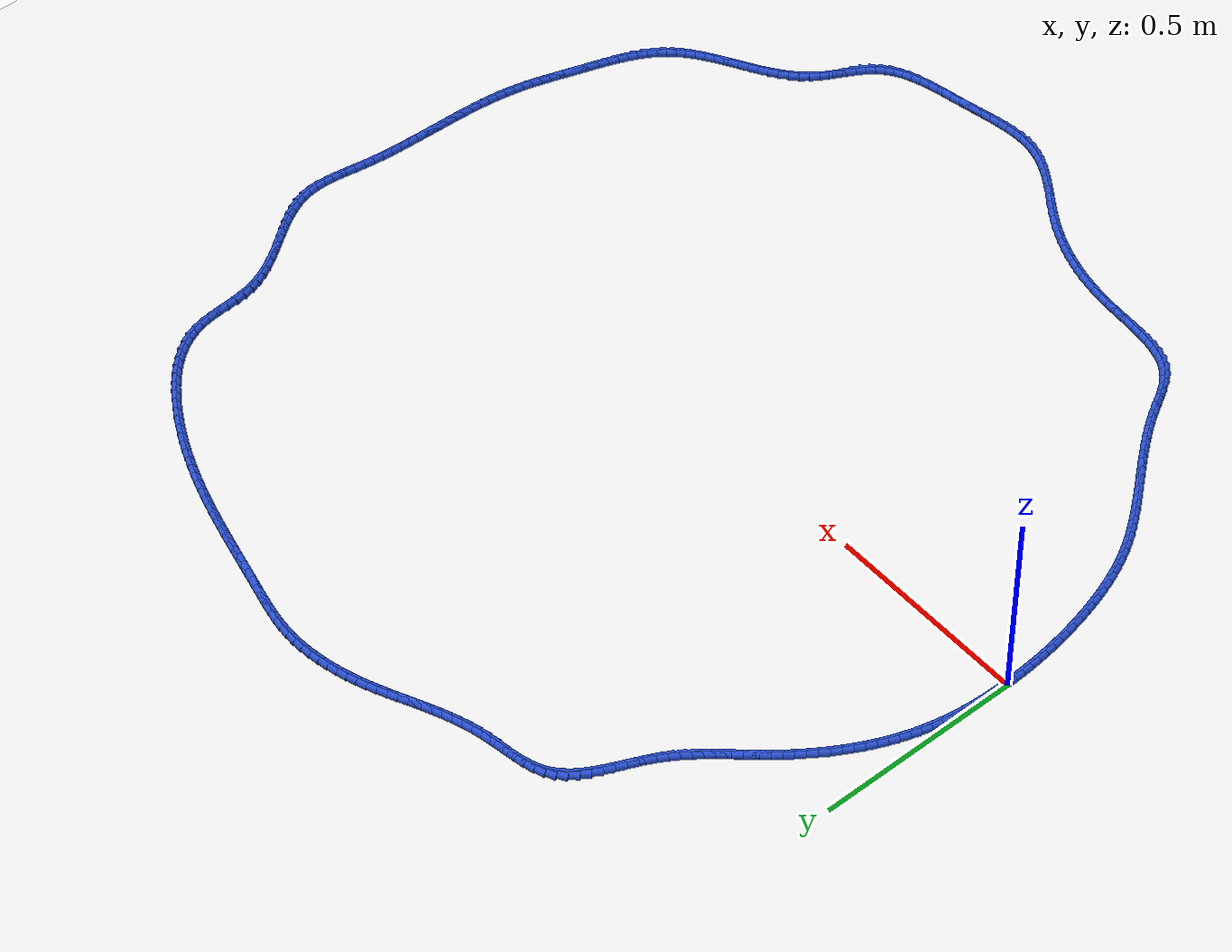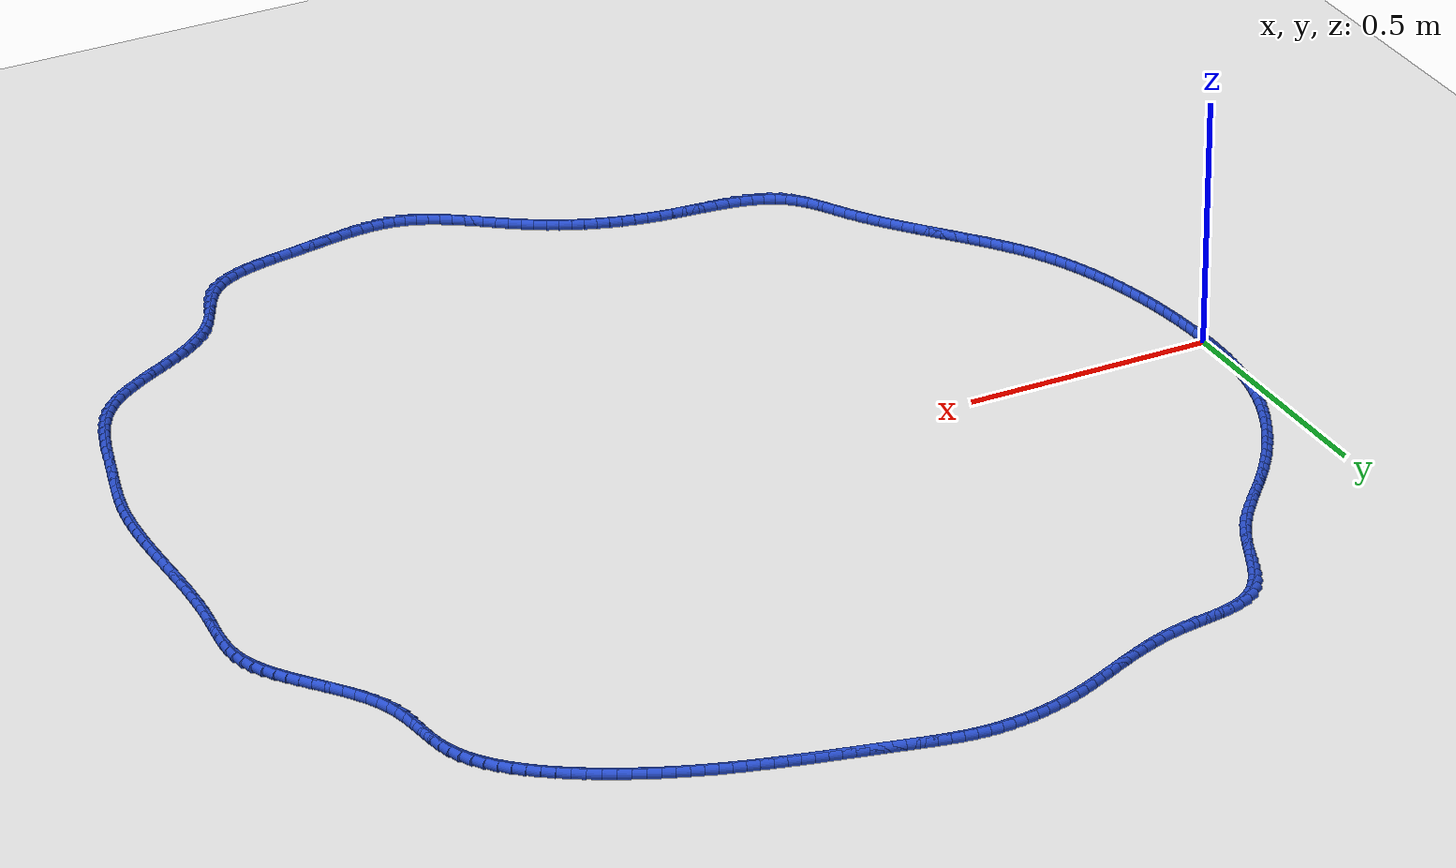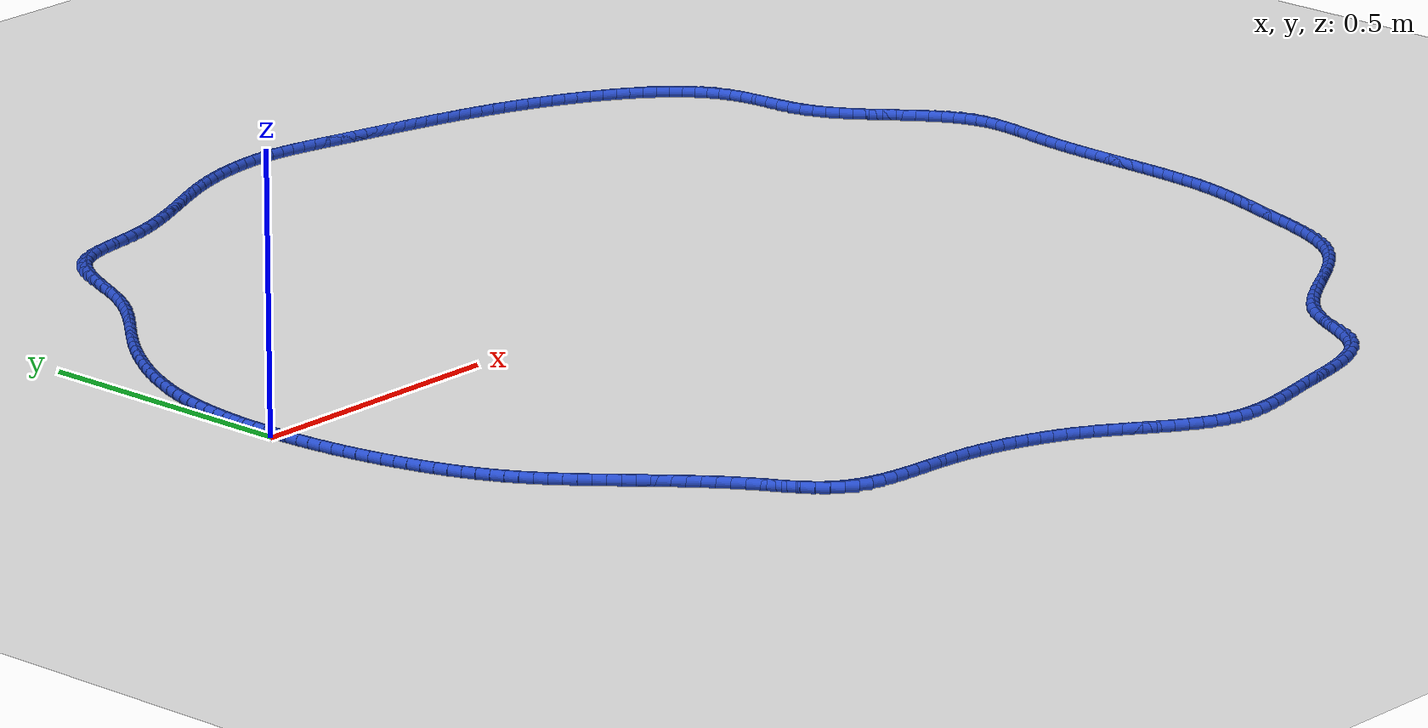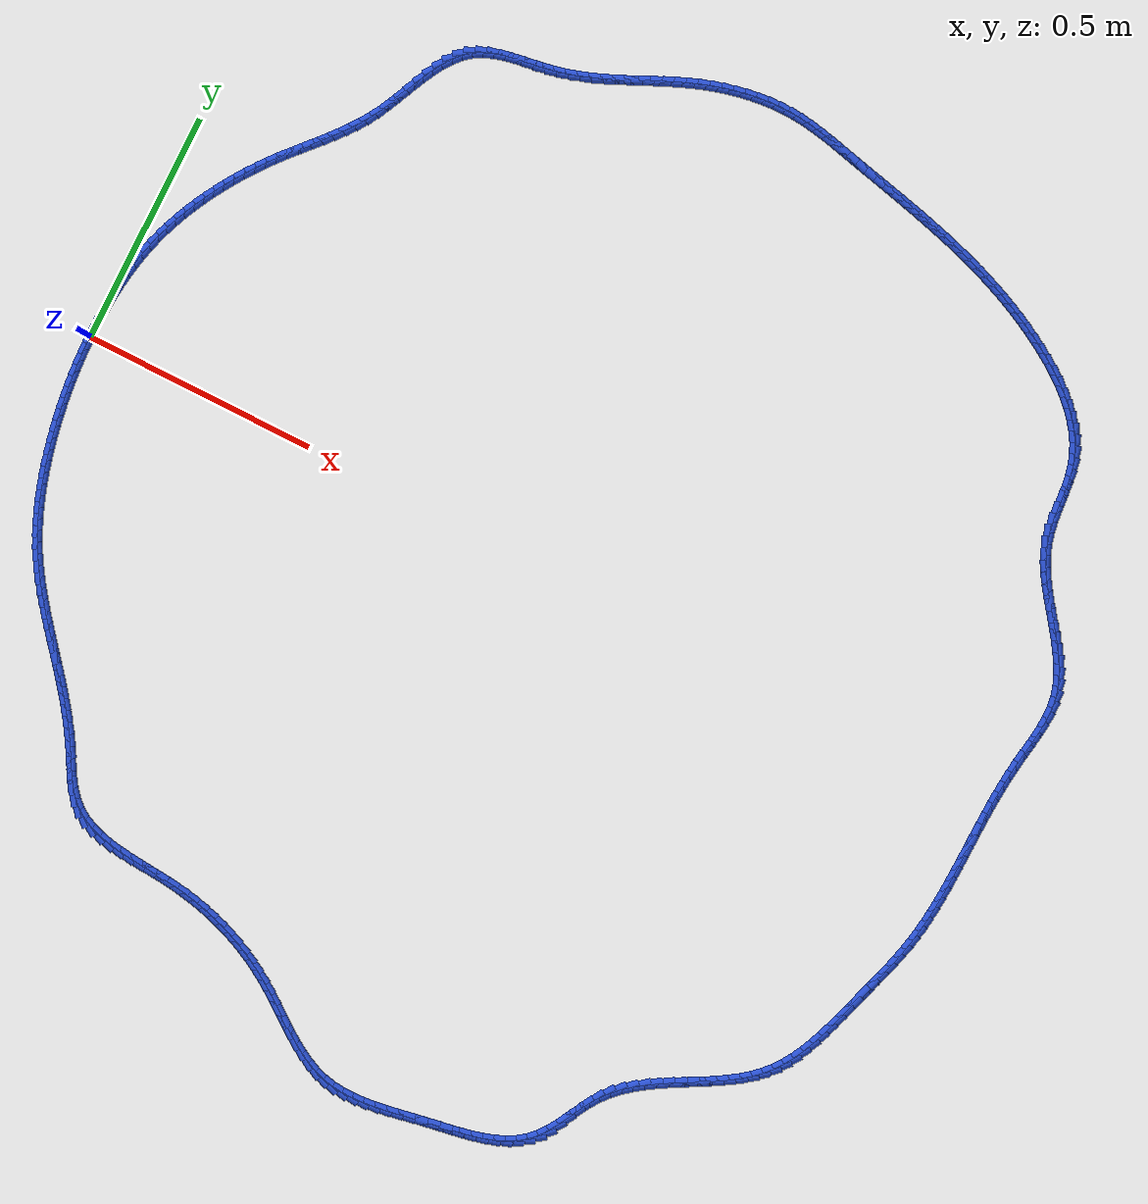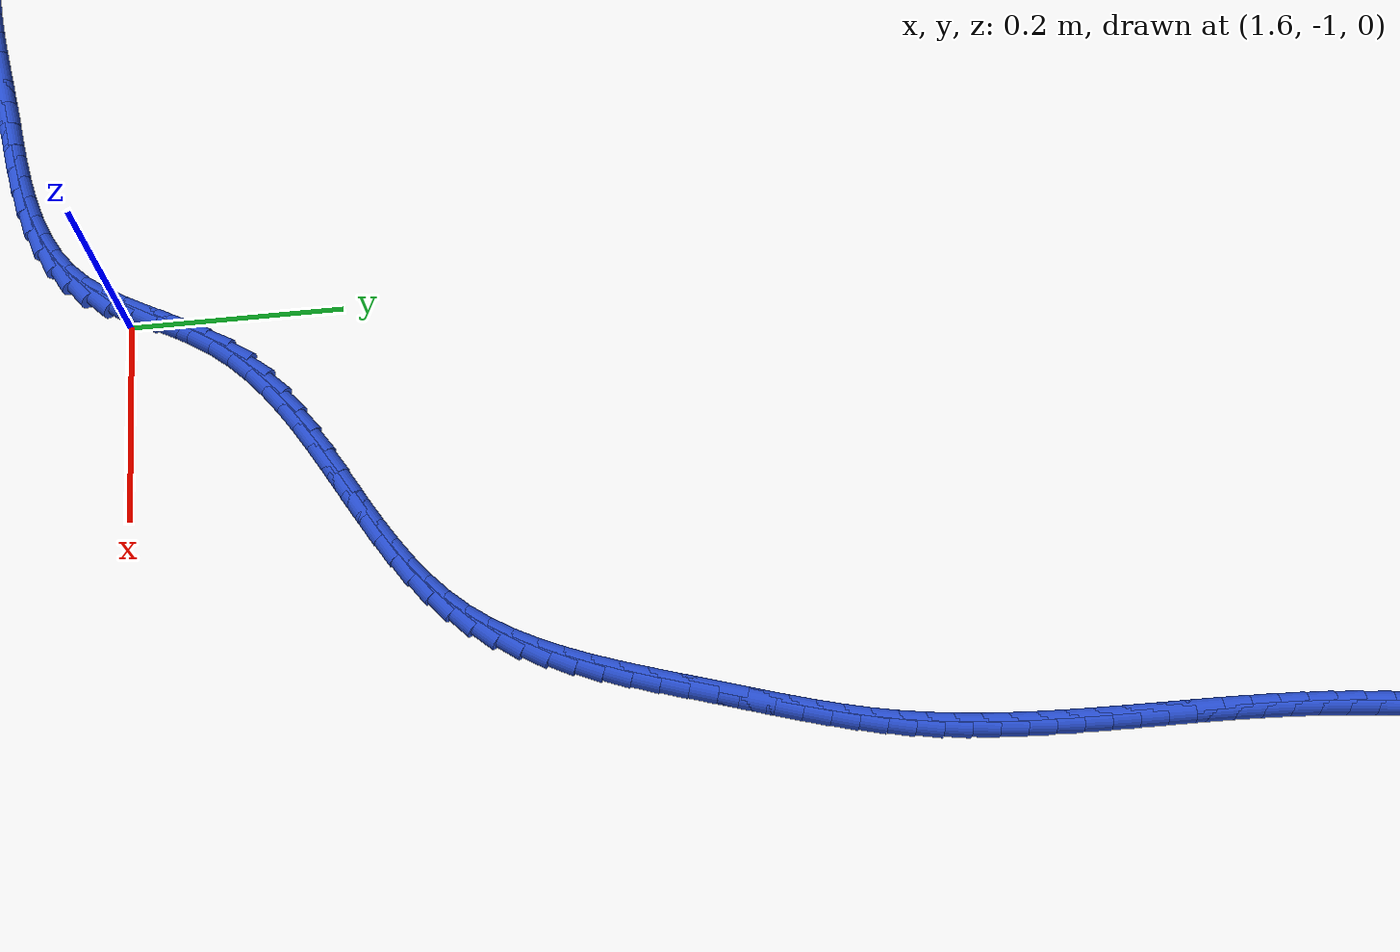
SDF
<sdf version="1.6">
 <world name="default">
  <light name="sun" type="directional">
   <pose>0 0 10 0 -0 0</pose>
   <diffuse>0.8 0.8 0.8 1</diffuse>
   <specular>0.2 0.2 0.2 1</specular>
   <attenuation>
    <range>1000</range>
    <constant>0.9</constant>
    <linear>0.01</linear>
    <quadratic>0.001</quadratic>
   </attenuation>
   <direction>-0.5 0.1 -0.9</direction>
  </light>
  <model name="ground_plane">
   <static>1</static>
   <link name="link">
    <collision name="collision">
     <geometry><plane><normal>0 0 1</normal><size>100 100</size></plane></geometry>
     <surface><friction><ode><mu>100</mu><mu2>50</mu2></ode></friction></surface>
    </collision>
    <visual name="visual">
     <cast_shadows>0</cast_shadows>
     <geometry><plane><normal>0 0 1</normal><size>100 100</size></plane></geometry>
     <material>
      <script><uri>file://media/materials/scripts/gazebo.material</uri><name>Gazebo/WhiteGlow</name></script>
     </material>
    </visual>
   </link>
  </model>
  <gravity>0 0 -9.8</gravity>
  <magnetic_field>6e-06 2.3e-05 -4.2e-05</magnetic_field>
  <atmosphere type="adiabatic"/>
  <physics name="default_physics" default="0" type="ode">
   <max_step_size>0.001</max_step_size>
   <real_time_factor>1</real_time_factor>
   <real_time_update_rate>1000</real_time_update_rate>
  </physics>
  <scene><ambient>0.4 0.4 0.4 1</ambient><background>0.7 0.7 0.7 1</background><shadows>1</shadows></scene>
  <spherical_coordinates>
   <surface_model>EARTH_WGS84</surface_model>
   <latitude_deg>0</latitude_deg>
   <longitude_deg>0</longitude_deg>
   <elevation>0</elevation>
   <heading_deg>0</heading_deg>
  </spherical_coordinates>
  <model name="line">
   <link name="link_0">
    <pose>-3.469446951953614e-18 -6.938893903907228e-18 0.01 0 1.57 -1.5668092946791665</pose>
    <collision name="collision">
     <geometry><cylinder><radius>0.01</radius><length>0.08</length></cylinder></geometry>
    </collision>
    <visual name="visual">
     <material>
      <script><name>Gazebo/Blue</name><uri>file://media/materials/scripts/gazebo.material</uri></script>
     </material>
     <geometry><cylinder><radius>0.01</radius><length>0.08</length></cylinder></geometry>
    </visual>
   </link>
   <link name="link_1">
    <pose>-9.668770848406657e-05 0.024250418192624773 0.01 0 1.57 1.5519842807327624</pose>
    <collision name="collision">
     <geometry><cylinder><radius>0.01</radius><length>0.08</length></cylinder></geometry>
    </collision>
    <visual name="visual">
     <material>
      <script><name>Gazebo/Blue</name><uri>file://media/materials/scripts/gazebo.material</uri></script>
     </material>
     <geometry><cylinder><radius>0.01</radius><length>0.08</length></cylinder></geometry>
    </visual>
   </link>
   <link name="link_2">
    <pose>0.00035997045068854154 0.048522328170225275 0.01 0 1.57 1.5270778236447393</pose>
    <collision name="collision">
     <geometry><cylinder><radius>0.01</radius><length>0.08</length></cylinder></geometry>
    </collision>
    <visual name="visual">
     <material>
      <script><name>Gazebo/Blue</name><uri>file://media/materials/scripts/gazebo.material</uri></script>
     </material>
     <geometry><cylinder><radius>0.01</radius><length>0.08</length></cylinder></geometry>
    </visual>
   </link>
   <link name="link_3">
    <pose>0.0014212684066295792 0.07278257584016903 0.01 0 1.57 1.5000000762777668</pose>
    <collision name="collision">
     <geometry><cylinder><radius>0.01</radius><length>0.08</length></cylinder></geometry>
    </collision>
    <visual name="visual">
     <material>
      <script><name>Gazebo/Blue</name><uri>file://media/materials/scripts/gazebo.material</uri></script>
     </material>
     <geometry><cylinder><radius>0.01</radius><length>0.08</length></cylinder></geometry>
    </visual>
   </link>
   <link name="link_4">
    <pose>0.0031385000884508072 0.09699800710982365 0.01 0 1.57 1.470688244465977</pose>
    <collision name="collision">
     <geometry><cylinder><radius>0.01</radius><length>0.08</length></cylinder></geometry>
    </collision>
    <visual name="visual">
     <material>
      <script><name>Gazebo/Blue</name><uri>file://media/materials/scripts/gazebo.material</uri></script>
     </material>
     <geometry><cylinder><radius>0.01</radius><length>0.08</length></cylinder></geometry>
    </visual>
   </link>
   <link name="link_5">
    <pose>0.005562959425263985 0.12113546788655669 0.01 0 1.57 1.439084465270947</pose>
    <collision name="collision">
     <geometry><cylinder><radius>0.01</radius><length>0.08</length></cylinder></geometry>
    </collision>
    <visual name="visual">
     <material>
      <script><name>Gazebo/Blue</name><uri>file://media/materials/scripts/gazebo.material</uri></script>
     </material>
     <geometry><cylinder><radius>0.01</radius><length>0.08</length></cylinder></geometry>
    </visual>
   </link>
   <link name="link_6">
    <pose>0.008745940346180871 0.14516180407773566 0.01 0 1.57 1.4051403267500029</pose>
    <collision name="collision">
     <geometry><cylinder><radius>0.01</radius><length>0.08</length></cylinder></geometry>
    </collision>
    <visual name="visual">
     <material>
      <script><name>Gazebo/Blue</name><uri>file://media/materials/scripts/gazebo.material</uri></script>
     </material>
     <geometry><cylinder><radius>0.01</radius><length>0.08</length></cylinder></geometry>
    </visual>
   </link>
   <link name="link_7">
    <pose>0.012738736780313228 0.16904386159072818 0.01 0 1.57 1.368822113248768</pose>
    <collision name="collision">
     <geometry><cylinder><radius>0.01</radius><length>0.08</length></cylinder></geometry>
    </collision>
    <visual name="visual">
     <material>
      <script><name>Gazebo/Blue</name><uri>file://media/materials/scripts/gazebo.material</uri></script>
     </material>
     <geometry><cylinder><radius>0.01</radius><length>0.08</length></cylinder></geometry>
    </visual>
   </link>
   <link name="link_8">
    <pose>0.01759264265677282 0.19274848633290176 0.01 0 1.57 1.3301167178738849</pose>
    <collision name="collision">
     <geometry><cylinder><radius>0.01</radius><length>0.08</length></cylinder></geometry>
    </collision>
    <visual name="visual">
     <material>
      <script><name>Gazebo/Blue</name><uri>file://media/materials/scripts/gazebo.material</uri></script>
     </material>
     <geometry><cylinder><radius>0.01</radius><length>0.08</length></cylinder></geometry>
    </visual>
   </link>
   <link name="link_9">
    <pose>0.023358951904671386 0.21624252421162393 0.01 0 1.57 1.2892994654592975</pose>
    <collision name="collision">
     <geometry><cylinder><radius>0.01</radius><length>0.08</length></cylinder></geometry>
    </collision>
    <visual name="visual">
     <material>
      <script><name>Gazebo/Blue</name><uri>file://media/materials/scripts/gazebo.material</uri></script>
     </material>
     <geometry><cylinder><radius>0.01</radius><length>0.08</length></cylinder></geometry>
    </visual>
   </link>
   <link name="link_10">
    <pose>0.030082690617742054 0.23949392359543983 0.01 0 1.57 1.2488211043745432</pose>
    <collision name="collision">
     <geometry><cylinder><radius>0.01</radius><length>0.08</length></cylinder></geometry>
    </collision>
    <visual name="visual">
     <material>
      <script><name>Gazebo/Blue</name><uri>file://media/materials/scripts/gazebo.material</uri></script>
     </material>
     <geometry><cylinder><radius>0.01</radius><length>0.08</length></cylinder></geometry>
    </visual>
   </link>
   <link name="link_11">
    <pose>0.03775074137843482 0.2624808598228182 0.01 0 1.57 1.2099850160552432</pose>
    <collision name="collision">
     <geometry><cylinder><radius>0.01</radius><length>0.08</length></cylinder></geometry>
    </collision>
    <visual name="visual">
     <material>
      <script><name>Gazebo/Blue</name><uri>file://media/materials/scripts/gazebo.material</uri></script>
     </material>
     <geometry><cylinder><radius>0.01</radius><length>0.08</length></cylinder></geometry>
    </visual>
   </link>
   <link name="link_12">
    <pose>0.04631845590246985 0.2851870542547955 0.01 0 1.57 1.1727685198565179</pose>
    <collision name="collision">
     <geometry><cylinder><radius>0.01</radius><length>0.08</length></cylinder></geometry>
    </collision>
    <visual name="visual">
     <material>
      <script><name>Gazebo/Blue</name><uri>file://media/materials/scripts/gazebo.material</uri></script>
     </material>
     <geometry><cylinder><radius>0.01</radius><length>0.08</length></cylinder></geometry>
    </visual>
   </link>
   <link name="link_13">
    <pose>0.05574087382757215 0.3075962831443847 0.01 0 1.57 1.1371211900026525</pose>
    <collision name="collision">
     <geometry><cylinder><radius>0.01</radius><length>0.08</length></cylinder></geometry>
    </collision>
    <visual name="visual">
     <material>
      <script><name>Gazebo/Blue</name><uri>file://media/materials/scripts/gazebo.material</uri></script>
     </material>
     <geometry><cylinder><radius>0.01</radius><length>0.08</length></cylinder></geometry>
    </visual>
   </link>
   <link name="link_14">
    <pose>0.06597303479146674 0.32969232274459914 0.01 0 1.57 1.1029811296559364</pose>
    <collision name="collision">
     <geometry><cylinder><radius>0.01</radius><length>0.08</length></cylinder></geometry>
    </collision>
    <visual name="visual">
     <material>
      <script><name>Gazebo/Blue</name><uri>file://media/materials/scripts/gazebo.material</uri></script>
     </material>
     <geometry><cylinder><radius>0.01</radius><length>0.08</length></cylinder></geometry>
    </visual>
   </link>
   <link name="link_15">
    <pose>0.07696997843187864 0.35145894930845145 0.01 0 1.57 1.0702778177255967</pose>
    <collision name="collision">
     <geometry><cylinder><radius>0.01</radius><length>0.08</length></cylinder></geometry>
    </collision>
    <visual name="visual">
     <material>
      <script><name>Gazebo/Blue</name><uri>file://media/materials/scripts/gazebo.material</uri></script>
     </material>
     <geometry><cylinder><radius>0.01</radius><length>0.08</length></cylinder></geometry>
    </visual>
   </link>
   <link name="link_16">
    <pose>0.08868674438653286 0.3728799390889551 0.01 0 1.57 1.038934515289923</pose>
    <collision name="collision">
     <geometry><cylinder><radius>0.01</radius><length>0.08</length></cylinder></geometry>
    </collision>
    <visual name="visual">
     <material>
      <script><name>Gazebo/Blue</name><uri>file://media/materials/scripts/gazebo.material</uri></script>
     </material>
     <geometry><cylinder><radius>0.01</radius><length>0.08</length></cylinder></geometry>
    </visual>
   </link>
   <link name="link_17">
    <pose>0.10107837229315449 0.3939390683391231 0.01 0 1.57 1.008870235082473</pose>
    <collision name="collision">
     <geometry><cylinder><radius>0.01</radius><length>0.08</length></cylinder></geometry>
    </collision>
    <visual name="visual">
     <material>
      <script><name>Gazebo/Blue</name><uri>file://media/materials/scripts/gazebo.material</uri></script>
     </material>
     <geometry><cylinder><radius>0.01</radius><length>0.08</length></cylinder></geometry>
    </visual>
   </link>
   <link name="link_18">
    <pose>0.1140999017894685 0.4146201133119686 0.01 0 1.57 0.9800012986721532</pose>
    <collision name="collision">
     <geometry><cylinder><radius>0.01</radius><length>0.08</length></cylinder></geometry>
    </collision>
    <visual name="visual">
     <material>
      <script><name>Gazebo/Blue</name><uri>file://media/materials/scripts/gazebo.material</uri></script>
     </material>
     <geometry><cylinder><radius>0.01</radius><length>0.08</length></cylinder></geometry>
    </visual>
   </link>
   <link name="link_19">
    <pose>0.12770637251319994 0.4349068502605046 0.01 0 1.57 0.9522425177753259</pose>
    <collision name="collision">
     <geometry><cylinder><radius>0.01</radius><length>0.08</length></cylinder></geometry>
    </collision>
    <visual name="visual">
     <material>
      <script><name>Gazebo/Blue</name><uri>file://media/materials/scripts/gazebo.material</uri></script>
     </material>
     <geometry><cylinder><radius>0.01</radius><length>0.08</length></cylinder></geometry>
    </visual>
   </link>
   <link name="link_20">
    <pose>0.14185282410207378 0.4547830554377442 0.01 0 1.57 0.9255080408733608</pose>
    <collision name="collision">
     <geometry><cylinder><radius>0.01</radius><length>0.08</length></cylinder></geometry>
    </collision>
    <visual name="visual">
     <material>
      <script><name>Gazebo/Blue</name><uri>file://media/materials/scripts/gazebo.material</uri></script>
     </material>
     <geometry><cylinder><radius>0.01</radius><length>0.08</length></cylinder></geometry>
    </visual>
   </link>
   <link name="link_21">
    <pose>0.1564942961938151 0.47423250509670056 0.01 0 1.57 0.8997119060340567</pose>
    <collision name="collision">
     <geometry><cylinder><radius>0.01</radius><length>0.08</length></cylinder></geometry>
    </collision>
    <visual name="visual">
     <material>
      <script><name>Gazebo/Blue</name><uri>file://media/materials/scripts/gazebo.material</uri></script>
     </material>
     <geometry><cylinder><radius>0.01</radius><length>0.08</length></cylinder></geometry>
    </visual>
   </link>
   <link name="link_22">
    <pose>0.17158582842614895 0.49323897549038664 0.01 0 1.57 0.8748506183977571</pose>
    <collision name="collision">
     <geometry><cylinder><radius>0.01</radius><length>0.08</length></cylinder></geometry>
    </collision>
    <visual name="visual">
     <material>
      <script><name>Gazebo/Blue</name><uri>file://media/materials/scripts/gazebo.material</uri></script>
     </material>
     <geometry><cylinder><radius>0.01</radius><length>0.08</length></cylinder></geometry>
    </visual>
   </link>
   <link name="link_23">
    <pose>0.18708140227971518 0.511788078097146 0.01 0 1.57 0.8544965456955175</pose>
    <collision name="collision">
     <geometry><cylinder><radius>0.01</radius><length>0.08</length></cylinder></geometry>
    </collision>
    <visual name="visual">
     <material>
      <script><name>Gazebo/Blue</name><uri>file://media/materials/scripts/gazebo.material</uri></script>
     </material>
     <geometry><cylinder><radius>0.01</radius><length>0.08</length></cylinder></geometry>
    </visual>
   </link>
   <link name="link_24">
    <pose>0.20288858191789733 0.5299459287340376 0.01 0 1.57 0.8437326135148264</pose>
    <collision name="collision">
     <geometry><cylinder><radius>0.01</radius><length>0.08</length></cylinder></geometry>
    </collision>
    <visual name="visual">
     <material>
      <script><name>Gazebo/Blue</name><uri>file://media/materials/scripts/gazebo.material</uri></script>
     </material>
     <geometry><cylinder><radius>0.01</radius><length>0.08</length></cylinder></geometry>
    </visual>
   </link>
   <link name="link_25">
    <pose>0.2188513869444735 0.5478888523610089 0.01 0 1.57 0.8430376336138947</pose>
    <collision name="collision">
     <geometry><cylinder><radius>0.01</radius><length>0.08</length></cylinder></geometry>
    </collision>
    <visual name="visual">
     <material>
      <script><name>Gazebo/Blue</name><uri>file://media/materials/scripts/gazebo.material</uri></script>
     </material>
     <geometry><cylinder><radius>0.01</radius><length>0.08</length></cylinder></geometry>
    </visual>
   </link>
   <link name="link_26">
    <pose>0.23480924708758877 0.5658011344347458 0.01 0 1.57 0.8524474503521972</pose>
    <collision name="collision">
     <geometry><cylinder><radius>0.01</radius><length>0.08</length></cylinder></geometry>
    </collision>
    <visual name="visual">
     <material>
      <script><name>Gazebo/Blue</name><uri>file://media/materials/scripts/gazebo.material</uri></script>
     </material>
     <geometry><cylinder><radius>0.01</radius><length>0.08</length></cylinder></geometry>
    </visual>
   </link>
   <link name="link_27">
    <pose>0.25060159207538807 0.5838670604119339 0.01 0 1.57 0.8719128689359373</pose>
    <collision name="collision">
     <geometry><cylinder><radius>0.01</radius><length>0.08</length></cylinder></geometry>
    </collision>
    <visual name="visual">
     <material>
      <script><name>Gazebo/Blue</name><uri>file://media/materials/scripts/gazebo.material</uri></script>
     </material>
     <geometry><cylinder><radius>0.01</radius><length>0.08</length></cylinder></geometry>
    </visual>
   </link>
   <link name="link_28">
    <pose>0.26606785163601654 0.6022709157492596 0.01 0 1.57 0.9012722103933641</pose>
    <collision name="collision">
     <geometry><cylinder><radius>0.01</radius><length>0.08</length></cylinder></geometry>
    </collision>
    <visual name="visual">
     <material>
      <script><name>Gazebo/Blue</name><uri>file://media/materials/scripts/gazebo.material</uri></script>
     </material>
     <geometry><cylinder><radius>0.01</radius><length>0.08</length></cylinder></geometry>
    </visual>
   </link>
   <link name="link_29">
    <pose>0.28104745549761906 0.6211969859034085 0.01 0 1.57 0.9401985837215712</pose>
    <collision name="collision">
     <geometry><cylinder><radius>0.01</radius><length>0.08</length></cylinder></geometry>
    </collision>
    <visual name="visual">
     <material>
      <script><name>Gazebo/Blue</name><uri>file://media/materials/scripts/gazebo.material</uri></script>
     </material>
     <geometry><cylinder><radius>0.01</radius><length>0.08</length></cylinder></geometry>
    </visual>
   </link>
   <link name="link_30">
    <pose>0.2953798333883409 0.640829556331067 0.01 0 1.57 0.9881307462801164</pose>
    <collision name="collision">
     <geometry><cylinder><radius>0.01</radius><length>0.08</length></cylinder></geometry>
    </collision>
    <visual name="visual">
     <material>
      <script><name>Gazebo/Blue</name><uri>file://media/materials/scripts/gazebo.material</uri></script>
     </material>
     <geometry><cylinder><radius>0.01</radius><length>0.08</length></cylinder></geometry>
    </visual>
   </link>
   <link name="link_31">
    <pose>0.3089044150363268 0.6613529124889203 0.01 0 1.57 1.0441260735722115</pose>
    <collision name="collision">
     <geometry><cylinder><radius>0.01</radius><length>0.08</length></cylinder></geometry>
    </collision>
    <visual name="visual">
     <material>
      <script><name>Gazebo/Blue</name><uri>file://media/materials/scripts/gazebo.material</uri></script>
     </material>
     <geometry><cylinder><radius>0.01</radius><length>0.08</length></cylinder></geometry>
    </visual>
   </link>
   <link name="link_32">
    <pose>0.3214619400428342 0.6829497191318804 0.01 0 1.57 1.0975435108582867</pose>
    <collision name="collision">
     <geometry><cylinder><radius>0.01</radius><length>0.08</length></cylinder></geometry>
    </collision>
    <visual name="visual">
     <material>
      <script><name>Gazebo/Blue</name><uri>file://media/materials/scripts/gazebo.material</uri></script>
     </material>
     <geometry><cylinder><radius>0.01</radius><length>0.08</length></cylinder></geometry>
    </visual>
   </link>
   <link name="link_33">
    <pose>0.33305902299179746 0.7055974044341369 0.01 0 1.57 1.130329600358164</pose>
    <collision name="collision">
     <geometry><cylinder><radius>0.01</radius><length>0.08</length></cylinder></geometry>
    </collision>
    <visual name="visual">
     <material>
      <script><name>Gazebo/Blue</name><uri>file://media/materials/scripts/gazebo.material</uri></script>
     </material>
     <geometry><cylinder><radius>0.01</radius><length>0.08</length></cylinder></geometry>
    </visual>
   </link>
   <link name="link_34">
    <pose>0.34402848020659565 0.7288697882104459 0.01 0 1.57 1.1418536177287364</pose>
    <collision name="collision">
     <geometry><cylinder><radius>0.01</radius><length>0.08</length></cylinder></geometry>
    </collision>
    <visual name="visual">
     <material>
      <script><name>Gazebo/Blue</name><uri>file://media/materials/scripts/gazebo.material</uri></script>
     </material>
     <geometry><cylinder><radius>0.01</radius><length>0.08</length></cylinder></geometry>
    </visual>
   </link>
   <link name="link_35">
    <pose>0.35474117768465696 0.752293611536665 0.01 0 1.57 1.132539995785431</pose>
    <collision name="collision">
     <geometry><cylinder><radius>0.01</radius><length>0.08</length></cylinder></geometry>
    </collision>
    <visual name="visual">
     <material>
      <script><name>Gazebo/Blue</name><uri>file://media/materials/scripts/gazebo.material</uri></script>
     </material>
     <geometry><cylinder><radius>0.01</radius><length>0.08</length></cylinder></geometry>
    </visual>
   </link>
   <link name="link_36">
    <pose>0.3655679814234096 0.775395615488651 0.01 0 1.57 1.1014872174678245</pose>
    <collision name="collision">
     <geometry><cylinder><radius>0.01</radius><length>0.08</length></cylinder></geometry>
    </collision>
    <visual name="visual">
     <material>
      <script><name>Gazebo/Blue</name><uri>file://media/materials/scripts/gazebo.material</uri></script>
     </material>
     <geometry><cylinder><radius>0.01</radius><length>0.08</length></cylinder></geometry>
    </visual>
   </link>
   <link name="link_37">
    <pose>0.37687975742028146 0.797702541142261 0.01 0 1.57 1.0464499784861645</pose>
    <collision name="collision">
     <geometry><cylinder><radius>0.01</radius><length>0.08</length></cylinder></geometry>
    </collision>
    <visual name="visual">
     <material>
      <script><name>Gazebo/Blue</name><uri>file://media/materials/scripts/gazebo.material</uri></script>
     </material>
     <geometry><cylinder><radius>0.01</radius><length>0.08</length></cylinder></geometry>
    </visual>
   </link>
   <link name="link_38">
    <pose>0.3890473716727008 0.8187411295733524 0.01 0 1.57 0.9640314212186265</pose>
    <collision name="collision">
     <geometry><cylinder><radius>0.01</radius><length>0.08</length></cylinder></geometry>
    </collision>
    <visual name="visual">
     <material>
      <script><name>Gazebo/Blue</name><uri>file://media/materials/scripts/gazebo.material</uri></script>
     </material>
     <geometry><cylinder><radius>0.01</radius><length>0.08</length></cylinder></geometry>
    </visual>
   </link>
   <link name="link_39">
    <pose>0.4024416901780958 0.8380381218577823 0.01 0 1.57 0.8504756450179841</pose>
    <collision name="collision">
     <geometry><cylinder><radius>0.01</radius><length>0.08</length></cylinder></geometry>
    </collision>
    <visual name="visual">
     <material>
      <script><name>Gazebo/Blue</name><uri>file://media/materials/scripts/gazebo.material</uri></script>
     </material>
     <geometry><cylinder><radius>0.01</radius><length>0.08</length></cylinder></geometry>
    </visual>
   </link>
   <link name="link_40">
    <pose>0.4174335789338943 0.8551202590714075 0.01 0 1.57 0.7037318500427051</pose>
    <collision name="collision">
     <geometry><cylinder><radius>0.01</radius><length>0.08</length></cylinder></geometry>
    </collision>
    <visual name="visual">
     <material>
      <script><name>Gazebo/Blue</name><uri>file://media/materials/scripts/gazebo.material</uri></script>
     </material>
     <geometry><cylinder><radius>0.01</radius><length>0.08</length></cylinder></geometry>
    </visual>
   </link>
   <link name="link_41">
    <pose>0.4343939039375247 0.8695142822900852 0.01 0 1.57 0.5318612919687798</pose>
    <collision name="collision">
     <geometry><cylinder><radius>0.01</radius><length>0.08</length></cylinder></geometry>
    </collision>
    <visual name="visual">
     <material>
      <script><name>Gazebo/Blue</name><uri>file://media/materials/scripts/gazebo.material</uri></script>
     </material>
     <geometry><cylinder><radius>0.01</radius><length>0.08</length></cylinder></geometry>
    </visual>
   </link>
   <link name="link_42">
    <pose>0.4536304416415753 0.8808334461201939 0.01 0 1.57 0.38193620138623197</pose>
    <collision name="collision">
     <geometry><cylinder><radius>0.01</radius><length>0.08</length></cylinder></geometry>
    </collision>
    <visual name="visual">
     <material>
      <script><name>Gazebo/Blue</name><uri>file://media/materials/scripts/gazebo.material</uri></script>
     </material>
     <geometry><cylinder><radius>0.01</radius><length>0.08</length></cylinder></geometry>
    </visual>
   </link>
   <link name="link_43">
    <pose>0.47493946596729103 0.8893924191657804 0.01 0 1.57 0.2743661039947238</pose>
    <collision name="collision">
     <geometry><cylinder><radius>0.01</radius><length>0.08</length></cylinder></geometry>
    </collision>
    <visual name="visual">
     <material>
      <script><name>Gazebo/Blue</name><uri>file://media/materials/scripts/gazebo.material</uri></script>
     </material>
     <geometry><cylinder><radius>0.01</radius><length>0.08</length></cylinder></geometry>
    </visual>
   </link>
   <link name="link_44">
    <pose>0.4978690154981541 0.8958462705762523 0.01 0 1.57 0.2048364941718794</pose>
    <collision name="collision">
     <geometry><cylinder><radius>0.01</radius><length>0.08</length></cylinder></geometry>
    </collision>
    <visual name="visual">
     <material>
      <script><name>Gazebo/Blue</name><uri>file://media/materials/scripts/gazebo.material</uri></script>
     </material>
     <geometry><cylinder><radius>0.01</radius><length>0.08</length></cylinder></geometry>
    </visual>
   </link>
   <link name="link_45">
    <pose>0.5219654885043072 0.9008523188324783 0.01 0 1.57 0.16830782976975128</pose>
    <collision name="collision">
     <geometry><cylinder><radius>0.01</radius><length>0.08</length></cylinder></geometry>
    </collision>
    <visual name="visual">
     <material>
      <script><name>Gazebo/Blue</name><uri>file://media/materials/scripts/gazebo.material</uri></script>
     </material>
     <geometry><cylinder><radius>0.01</radius><length>0.08</length></cylinder></geometry>
    </visual>
   </link>
   <link name="link_46">
    <pose>0.5467752832558944 0.905067882415328 0.01 0 1.57 0.16142615520135203</pose>
    <collision name="collision">
     <geometry><cylinder><radius>0.01</radius><length>0.08</length></cylinder></geometry>
    </collision>
    <visual name="visual">
     <material>
      <script><name>Gazebo/Blue</name><uri>file://media/materials/scripts/gazebo.material</uri></script>
     </material>
     <geometry><cylinder><radius>0.01</radius><length>0.08</length></cylinder></geometry>
    </visual>
   </link>
   <link name="link_47">
    <pose>0.5718447980230582 0.9091502798056699 0.01 0 1.57 0.18310891142201577</pose>
    <collision name="collision">
     <geometry><cylinder><radius>0.01</radius><length>0.08</length></cylinder></geometry>
    </collision>
    <visual name="visual">
     <material>
      <script><name>Gazebo/Blue</name><uri>file://media/materials/scripts/gazebo.material</uri></script>
     </material>
     <geometry><cylinder><radius>0.01</radius><length>0.08</length></cylinder></geometry>
    </visual>
   </link>
   <link name="link_48">
    <pose>0.5967204310759422 0.9137568294843734 0.01 0 1.57 0.23057755355342752</pose>
    <collision name="collision">
     <geometry><cylinder><radius>0.01</radius><length>0.08</length></cylinder></geometry>
    </collision>
    <visual name="visual">
     <material>
      <script><name>Gazebo/Blue</name><uri>file://media/materials/scripts/gazebo.material</uri></script>
     </material>
     <geometry><cylinder><radius>0.01</radius><length>0.08</length></cylinder></geometry>
    </visual>
   </link>
   <link name="link_49">
    <pose>0.6210060169898253 0.9194579354174544 0.01 0 1.57 0.2811419478961749</pose>
    <collision name="collision">
     <geometry><cylinder><radius>0.01</radius><length>0.08</length></cylinder></geometry>
    </collision>
    <visual name="visual">
     <material>
      <script><name>Gazebo/Blue</name><uri>file://media/materials/scripts/gazebo.material</uri></script>
     </material>
     <geometry><cylinder><radius>0.01</radius><length>0.08</length></cylinder></geometry>
    </visual>
   </link>
   <link name="link_50">
    <pose>0.6446591116681746 0.9262887387687698 0.01 0 1.57 0.3251660689453909</pose>
    <collision name="collision">
     <geometry><cylinder><radius>0.01</radius><length>0.08</length></cylinder></geometry>
    </collision>
    <visual name="visual">
     <material>
      <script><name>Gazebo/Blue</name><uri>file://media/materials/scripts/gazebo.material</uri></script>
     </material>
     <geometry><cylinder><radius>0.01</radius><length>0.08</length></cylinder></geometry>
    </visual>
   </link>
   <link name="link_51">
    <pose>0.6677718137486038 0.9340807861910443 0.01 0 1.57 0.36206194708063233</pose>
    <collision name="collision">
     <geometry><cylinder><radius>0.01</radius><length>0.08</length></cylinder></geometry>
    </collision>
    <visual name="visual">
     <material>
      <script><name>Gazebo/Blue</name><uri>file://media/materials/scripts/gazebo.material</uri></script>
     </material>
     <geometry><cylinder><radius>0.01</radius><length>0.08</length></cylinder></geometry>
    </visual>
   </link>
   <link name="link_52">
    <pose>0.6904364834495412 0.9426652285042689 0.01 0 1.57 0.39144726476501857</pose>
    <collision name="collision">
     <geometry><cylinder><radius>0.01</radius><length>0.08</length></cylinder></geometry>
    </collision>
    <visual name="visual">
     <material>
      <script><name>Gazebo/Blue</name><uri>file://media/materials/scripts/gazebo.material</uri></script>
     </material>
     <geometry><cylinder><radius>0.01</radius><length>0.08</length></cylinder></geometry>
    </visual>
   </link>
   <link name="link_53">
    <pose>0.7127454809894156 0.951873216528436 0.01 0 1.57 0.41308402396247024</pose>
    <collision name="collision">
     <geometry><cylinder><radius>0.01</radius><length>0.08</length></cylinder></geometry>
    </collision>
    <visual name="visual">
     <material>
      <script><name>Gazebo/Blue</name><uri>file://media/materials/scripts/gazebo.material</uri></script>
     </material>
     <geometry><cylinder><radius>0.01</radius><length>0.08</length></cylinder></geometry>
    </visual>
   </link>
   <link name="link_54">
    <pose>0.7347911665866551 0.9615359010835374 0.01 0 1.57 0.42683475521353026</pose>
    <collision name="collision">
     <geometry><cylinder><radius>0.01</radius><length>0.08</length></cylinder></geometry>
    </collision>
    <visual name="visual">
     <material>
      <script><name>Gazebo/Blue</name><uri>file://media/materials/scripts/gazebo.material</uri></script>
     </material>
     <geometry><cylinder><radius>0.01</radius><length>0.08</length></cylinder></geometry>
    </visual>
   </link>
   <link name="link_55">
    <pose>0.7566659004596887 0.9714844329895649 0.01 0 1.57 0.43262606885576316</pose>
    <collision name="collision">
     <geometry><cylinder><radius>0.01</radius><length>0.08</length></cylinder></geometry>
    </collision>
    <visual name="visual">
     <material>
      <script><name>Gazebo/Blue</name><uri>file://media/materials/scripts/gazebo.material</uri></script>
     </material>
     <geometry><cylinder><radius>0.01</radius><length>0.08</length></cylinder></geometry>
    </visual>
   </link>
   <link name="link_56">
    <pose>0.7784620428269444 0.9815499630665101 0.01 0 1.57 0.4304240268984643</pose>
    <collision name="collision">
     <geometry><cylinder><radius>0.01</radius><length>0.08</length></cylinder></geometry>
    </collision>
    <visual name="visual">
     <material>
      <script><name>Gazebo/Blue</name><uri>file://media/materials/scripts/gazebo.material</uri></script>
     </material>
     <geometry><cylinder><radius>0.01</radius><length>0.08</length></cylinder></geometry>
    </visual>
   </link>
   <link name="link_57">
    <pose>0.8002719539068512 0.9915636421343657 0.01 0 1.57 0.42022355418391083</pose>
    <collision name="collision">
     <geometry><cylinder><radius>0.01</radius><length>0.08</length></cylinder></geometry>
    </collision>
    <visual name="visual">
     <material>
      <script><name>Gazebo/Blue</name><uri>file://media/materials/scripts/gazebo.material</uri></script>
     </material>
     <geometry><cylinder><radius>0.01</radius><length>0.08</length></cylinder></geometry>
    </visual>
   </link>
   <link name="link_58">
    <pose>0.8221879939178369 1.0013566210131222 0.01 0 1.57 0.40205273999950547</pose>
    <collision name="collision">
     <geometry><cylinder><radius>0.01</radius><length>0.08</length></cylinder></geometry>
    </collision>
    <visual name="visual">
     <material>
      <script><name>Gazebo/Blue</name><uri>file://media/materials/scripts/gazebo.material</uri></script>
     </material>
     <geometry><cylinder><radius>0.01</radius><length>0.08</length></cylinder></geometry>
    </visual>
   </link>
   <link name="link_59">
    <pose>0.8443025230783303 1.0107600505227723 0.01 0 1.57 0.3759919458420763</pose>
    <collision name="collision">
     <geometry><cylinder><radius>0.01</radius><length>0.08</length></cylinder></geometry>
    </collision>
    <visual name="visual">
     <material>
      <script><name>Gazebo/Blue</name><uri>file://media/materials/scripts/gazebo.material</uri></script>
     </material>
     <geometry><cylinder><radius>0.01</radius><length>0.08</length></cylinder></geometry>
    </visual>
   </link>
   <link name="link_60">
    <pose>0.86670790160676 1.019605081483308 0.01 0 1.57 0.3422551058739761</pose>
    <collision name="collision">
     <geometry><cylinder><radius>0.01</radius><length>0.08</length></cylinder></geometry>
    </collision>
    <visual name="visual">
     <material>
      <script><name>Gazebo/Blue</name><uri>file://media/materials/scripts/gazebo.material</uri></script>
     </material>
     <geometry><cylinder><radius>0.01</radius><length>0.08</length></cylinder></geometry>
    </visual>
   </link>
   <link name="link_61">
    <pose>0.8894951881271966 1.0277236492138477 0.01 0 1.57 0.3034129283103802</pose>
    <collision name="collision">
     <geometry><cylinder><radius>0.01</radius><length>0.08</length></cylinder></geometry>
    </collision>
    <visual name="visual">
     <material>
      <script><name>Gazebo/Blue</name><uri>file://media/materials/scripts/gazebo.material</uri></script>
     </material>
     <geometry><cylinder><radius>0.01</radius><length>0.08</length></cylinder></geometry>
    </visual>
   </link>
   <link name="link_62">
    <pose>0.9126918097679279 1.0349860411150384 0.01 0 1.57 0.2627217710958454</pose>
    <collision name="collision">
     <geometry><cylinder><radius>0.01</radius><length>0.08</length></cylinder></geometry>
    </collision>
    <visual name="visual">
     <material>
      <script><name>Gazebo/Blue</name><uri>file://media/materials/scripts/gazebo.material</uri></script>
     </material>
     <geometry><cylinder><radius>0.01</radius><length>0.08</length></cylinder></geometry>
    </visual>
   </link>
   <link name="link_63">
    <pose>0.9362340886363153 1.0413174555580602 0.01 0 1.57 0.22015469262808218</pose>
    <collision name="collision">
     <geometry><cylinder><radius>0.01</radius><length>0.08</length></cylinder></geometry>
    </collision>
    <visual name="visual">
     <material>
      <script><name>Gazebo/Blue</name><uri>file://media/materials/scripts/gazebo.material</uri></script>
     </material>
     <geometry><cylinder><radius>0.01</radius><length>0.08</length></cylinder></geometry>
    </visual>
   </link>
   <link name="link_64">
    <pose>0.9600513276982324 1.0466473215027872 0.01 0 1.57 0.17542535260177597</pose>
    <collision name="collision">
     <geometry><cylinder><radius>0.01</radius><length>0.08</length></cylinder></geometry>
    </collision>
    <visual name="visual">
     <material>
      <script><name>Gazebo/Blue</name><uri>file://media/materials/scripts/gazebo.material</uri></script>
     </material>
     <geometry><cylinder><radius>0.01</radius><length>0.08</length></cylinder></geometry>
    </visual>
   </link>
   <link name="link_65">
    <pose>0.9840728299195529 1.0509050679090928 0.01 0 1.57 0.1282528940160982</pose>
    <collision name="collision">
     <geometry><cylinder><radius>0.01</radius><length>0.08</length></cylinder></geometry>
    </collision>
    <visual name="visual">
     <material>
      <script><name>Gazebo/Blue</name><uri>file://media/materials/scripts/gazebo.material</uri></script>
     </material>
     <geometry><cylinder><radius>0.01</radius><length>0.08</length></cylinder></geometry>
    </visual>
   </link>
   <link name="link_66">
    <pose>1.008227898266151 1.0540201237368514 0.01 0 1.57 0.07836750552753674</pose>
    <collision name="collision">
     <geometry><cylinder><radius>0.01</radius><length>0.08</length></cylinder></geometry>
    </collision>
    <visual name="visual">
     <material>
      <script><name>Gazebo/Blue</name><uri>file://media/materials/scripts/gazebo.material</uri></script>
     </material>
     <geometry><cylinder><radius>0.01</radius><length>0.08</length></cylinder></geometry>
    </visual>
   </link>
   <link name="link_67">
    <pose>1.0324458357038997 1.0559219179459365 0.01 0 1.57 0.025519397075747997</pose>
    <collision name="collision">
     <geometry><cylinder><radius>0.01</radius><length>0.08</length></cylinder></geometry>
    </collision>
    <visual name="visual">
     <material>
      <script><name>Gazebo/Blue</name><uri>file://media/materials/scripts/gazebo.material</uri></script>
     </material>
     <geometry><cylinder><radius>0.01</radius><length>0.08</length></cylinder></geometry>
    </visual>
   </link>
   <link name="link_68">
    <pose>1.0566559451986737 1.056539879496222 0.01 0 1.57 -0.03050722279257772</pose>
    <collision name="collision">
     <geometry><cylinder><radius>0.01</radius><length>0.08</length></cylinder></geometry>
    </collision>
    <visual name="visual">
     <material>
      <script><name>Gazebo/Blue</name><uri>file://media/materials/scripts/gazebo.material</uri></script>
     </material>
     <geometry><cylinder><radius>0.01</radius><length>0.08</length></cylinder></geometry>
    </visual>
   </link>
   <link name="link_69">
    <pose>1.080787537617207 1.0558034631571953 0.01 0 1.57 -0.08710678217348848</pose>
    <collision name="collision">
     <geometry><cylinder><radius>0.01</radius><length>0.08</length></cylinder></geometry>
    </collision>
    <visual name="visual">
     <material>
      <script><name>Gazebo/Blue</name><uri>file://media/materials/scripts/gazebo.material</uri></script>
     </material>
     <geometry><cylinder><radius>0.01</radius><length>0.08</length></cylinder></geometry>
    </visual>
   </link>
   <link name="link_70">
    <pose>1.1047899032811292 1.0537073902544252 0.01 0 1.57 -0.13543388009078403</pose>
    <collision name="collision">
     <geometry><cylinder><radius>0.01</radius><length>0.08</length></cylinder></geometry>
    </collision>
    <visual name="visual">
     <material>
      <script><name>Gazebo/Blue</name><uri>file://media/materials/scripts/gazebo.material</uri></script>
     </material>
     <geometry><cylinder><radius>0.01</radius><length>0.08</length></cylinder></geometry>
    </visual>
   </link>
   <link name="link_71">
    <pose>1.1286754459439066 1.0504525537212743 0.01 0 1.57 -0.17358100366658533</pose>
    <collision name="collision">
     <geometry><cylinder><radius>0.01</radius><length>0.08</length></cylinder></geometry>
    </collision>
    <visual name="visual">
     <material>
      <script><name>Gazebo/Blue</name><uri>file://media/materials/scripts/gazebo.material</uri></script>
     </material>
     <geometry><cylinder><radius>0.01</radius><length>0.08</length></cylinder></geometry>
    </visual>
   </link>
   <link name="link_72">
    <pose>1.1524690013365628 1.046280457827342 0.01 0 1.57 -0.20154885319310645</pose>
    <collision name="collision">
     <geometry><cylinder><radius>0.01</radius><length>0.08</length></cylinder></geometry>
    </collision>
    <visual name="visual">
     <material>
      <script><name>Gazebo/Blue</name><uri>file://media/materials/scripts/gazebo.material</uri></script>
     </material>
     <geometry><cylinder><radius>0.01</radius><length>0.08</length></cylinder></geometry>
    </visual>
   </link>
   <link name="link_73">
    <pose>1.1761954051901238 1.0414326068422268 0.01 0 1.57 -0.21943212921030308</pose>
    <collision name="collision">
     <geometry><cylinder><radius>0.01</radius><length>0.08</length></cylinder></geometry>
    </collision>
    <visual name="visual">
     <material>
      <script><name>Gazebo/Blue</name><uri>file://media/materials/scripts/gazebo.material</uri></script>
     </material>
     <geometry><cylinder><radius>0.01</radius><length>0.08</length></cylinder></geometry>
    </visual>
   </link>
   <link name="link_74">
    <pose>1.1998794932356127 1.0361505050355284 0.01 0 1.57 -0.22733328139425454</pose>
    <collision name="collision">
     <geometry><cylinder><radius>0.01</radius><length>0.08</length></cylinder></geometry>
    </collision>
    <visual name="visual">
     <material>
      <script><name>Gazebo/Blue</name><uri>file://media/materials/scripts/gazebo.material</uri></script>
     </material>
     <geometry><cylinder><radius>0.01</radius><length>0.08</length></cylinder></geometry>
    </visual>
   </link>
   <link name="link_75">
    <pose>1.2235461012040543 1.0306756566768456 0.01 0 1.57 -0.2263782300799881</pose>
    <collision name="collision">
     <geometry><cylinder><radius>0.01</radius><length>0.08</length></cylinder></geometry>
    </collision>
    <visual name="visual">
     <material>
      <script><name>Gazebo/Blue</name><uri>file://media/materials/scripts/gazebo.material</uri></script>
     </material>
     <geometry><cylinder><radius>0.01</radius><length>0.08</length></cylinder></geometry>
    </visual>
   </link>
   <link name="link_76">
    <pose>1.2472163113289658 1.0252237858002047 0.01 0 1.57 -0.22391142568460923</pose>
    <collision name="collision">
     <geometry><cylinder><radius>0.01</radius><length>0.08</length></cylinder></geometry>
    </collision>
    <visual name="visual">
     <material>
      <script><name>Gazebo/Blue</name><uri>file://media/materials/scripts/gazebo.material</uri></script>
     </material>
     <geometry><cylinder><radius>0.01</radius><length>0.08</length></cylinder></geometry>
    </visual>
   </link>
   <link name="link_77">
    <pose>1.2708854351372145 1.019833614886543 0.01 0 1.57 -0.2230144385574613</pose>
    <collision name="collision">
     <geometry><cylinder><radius>0.01</radius><length>0.08</length></cylinder></geometry>
    </collision>
    <visual name="visual">
     <material>
      <script><name>Gazebo/Blue</name><uri>file://media/materials/scripts/gazebo.material</uri></script>
     </material>
     <geometry><cylinder><radius>0.01</radius><length>0.08</length></cylinder></geometry>
    </visual>
   </link>
   <link name="link_78">
    <pose>1.2945379618577029 1.0144695353721083 0.01 0 1.57 -0.22370138353793034</pose>
    <collision name="collision">
     <geometry><cylinder><radius>0.01</radius><length>0.08</length></cylinder></geometry>
    </collision>
    <visual name="visual">
     <material>
      <script><name>Gazebo/Blue</name><uri>file://media/materials/scripts/gazebo.material</uri></script>
     </material>
     <geometry><cylinder><radius>0.01</radius><length>0.08</length></cylinder></geometry>
    </visual>
   </link>
   <link name="link_79">
    <pose>1.318158343468812 1.009095682844519 0.01 0 1.57 -0.22597860267105793</pose>
    <collision name="collision">
     <geometry><cylinder><radius>0.01</radius><length>0.08</length></cylinder></geometry>
    </collision>
    <visual name="visual">
     <material>
      <script><name>Gazebo/Blue</name><uri>file://media/materials/scripts/gazebo.material</uri></script>
     </material>
     <geometry><cylinder><radius>0.01</radius><length>0.08</length></cylinder></geometry>
    </visual>
   </link>
   <link name="link_80">
    <pose>1.3417310319489253 1.0036761928913946 0.01 0 1.57 -0.2298552572701455</pose>
    <collision name="collision">
     <geometry><cylinder><radius>0.01</radius><length>0.08</length></cylinder></geometry>
    </collision>
    <visual name="visual">
     <material>
      <script><name>Gazebo/Blue</name><uri>file://media/materials/scripts/gazebo.material</uri></script>
     </material>
     <geometry><cylinder><radius>0.01</radius><length>0.08</length></cylinder></geometry>
    </visual>
   </link>
   <link name="link_81">
    <pose>1.3652404792764232 0.9981752011003525 0.01 0 1.57 -0.23534320088937022</pose>
    <collision name="collision">
     <geometry><cylinder><radius>0.01</radius><length>0.08</length></cylinder></geometry>
    </collision>
    <visual name="visual">
     <material>
      <script><name>Gazebo/Blue</name><uri>file://media/materials/scripts/gazebo.material</uri></script>
     </material>
     <geometry><cylinder><radius>0.01</radius><length>0.08</length></cylinder></geometry>
    </visual>
   </link>
   <link name="link_82">
    <pose>1.38867113742969 0.9925568430590116 0.01 0 1.57 -0.24245673517450567</pose>
    <collision name="collision">
     <geometry><cylinder><radius>0.01</radius><length>0.08</length></cylinder></geometry>
    </collision>
    <visual name="visual">
     <material>
      <script><name>Gazebo/Blue</name><uri>file://media/materials/scripts/gazebo.material</uri></script>
     </material>
     <geometry><cylinder><radius>0.01</radius><length>0.08</length></cylinder></geometry>
    </visual>
   </link>
   <link name="link_83">
    <pose>1.4120074583871063 0.9867852543549904 0.01 0 1.57 -0.25121223921615465</pose>
    <collision name="collision">
     <geometry><cylinder><radius>0.01</radius><length>0.08</length></cylinder></geometry>
    </collision>
    <visual name="visual">
     <material>
      <script><name>Gazebo/Blue</name><uri>file://media/materials/scripts/gazebo.material</uri></script>
     </material>
     <geometry><cylinder><radius>0.01</radius><length>0.08</length></cylinder></geometry>
    </visual>
   </link>
   <link name="link_84">
    <pose>1.4352338941270542 0.9808245705759071 0.01 0 1.57 -0.2616369609576843</pose>
    <collision name="collision">
     <geometry><cylinder><radius>0.01</radius><length>0.08</length></cylinder></geometry>
    </collision>
    <visual name="visual">
     <material>
      <script><name>Gazebo/Blue</name><uri>file://media/materials/scripts/gazebo.material</uri></script>
     </material>
     <geometry><cylinder><radius>0.01</radius><length>0.08</length></cylinder></geometry>
    </visual>
   </link>
   <link name="link_85">
    <pose>1.458337717522701 0.9746379416914022 0.01 0 1.57 -0.27378797087168233</pose>
    <collision name="collision">
     <geometry><cylinder><radius>0.01</radius><length>0.08</length></cylinder></geometry>
    </collision>
    <visual name="visual">
     <material>
      <script><name>Gazebo/Blue</name><uri>file://media/materials/scripts/gazebo.material</uri></script>
     </material>
     <geometry><cylinder><radius>0.01</radius><length>0.08</length></cylinder></geometry>
    </visual>
   </link>
   <link name="link_86">
    <pose>1.4813216268809255 0.9681831280391188 0.01 0 1.57 -0.2876615101169753</pose>
    <collision name="collision">
     <geometry><cylinder><radius>0.01</radius><length>0.08</length></cylinder></geometry>
    </collision>
    <visual name="visual">
     <material>
      <script><name>Gazebo/Blue</name><uri>file://media/materials/scripts/gazebo.material</uri></script>
     </material>
     <geometry><cylinder><radius>0.01</radius><length>0.08</length></cylinder></geometry>
    </visual>
   </link>
   <link name="link_87">
    <pose>1.50419356655007 0.9614160569947604 0.01 0 1.57 -0.30322206928134615</pose>
    <collision name="collision">
     <geometry><cylinder><radius>0.01</radius><length>0.08</length></cylinder></geometry>
    </collision>
    <visual name="visual">
     <material>
      <script><name>Gazebo/Blue</name><uri>file://media/materials/scripts/gazebo.material</uri></script>
     </material>
     <geometry><cylinder><radius>0.01</radius><length>0.08</length></cylinder></geometry>
    </visual>
   </link>
   <link name="link_88">
    <pose>1.52696148523075 0.9542926544133484 0.01 0 1.57 -0.3204211605542874</pose>
    <collision name="collision">
     <geometry><cylinder><radius>0.01</radius><length>0.08</length></cylinder></geometry>
    </collision>
    <visual name="visual">
     <material>
      <script><name>Gazebo/Blue</name><uri>file://media/materials/scripts/gazebo.material</uri></script>
     </material>
     <geometry><cylinder><radius>0.01</radius><length>0.08</length></cylinder></geometry>
    </visual>
   </link>
   <link name="link_89">
    <pose>1.5496333316235822 0.9467688461499053 0.01 0 1.57 -0.33919663083866486</pose>
    <collision name="collision">
     <geometry><cylinder><radius>0.01</radius><length>0.08</length></cylinder></geometry>
    </collision>
    <visual name="visual">
     <material>
      <script><name>Gazebo/Blue</name><uri>file://media/materials/scripts/gazebo.material</uri></script>
     </material>
     <geometry><cylinder><radius>0.01</radius><length>0.08</length></cylinder></geometry>
    </visual>
   </link>
   <link name="link_90">
    <pose>1.5722170544291822 0.9388005580594526 0.01 0 1.57 -0.3594721964824236</pose>
    <collision name="collision">
     <geometry><cylinder><radius>0.01</radius><length>0.08</length></cylinder></geometry>
    </collision>
    <visual name="visual">
     <material>
      <script><name>Gazebo/Blue</name><uri>file://media/materials/scripts/gazebo.material</uri></script>
     </material>
     <geometry><cylinder><radius>0.01</radius><length>0.08</length></cylinder></geometry>
    </visual>
   </link>
   <link name="link_91">
    <pose>1.5947206023481675 0.9303437159970125 0.01 0 1.57 -0.3811572939427457</pose>
    <collision name="collision">
     <geometry><cylinder><radius>0.01</radius><length>0.08</length></cylinder></geometry>
    </collision>
    <visual name="visual">
     <material>
      <script><name>Gazebo/Blue</name><uri>file://media/materials/scripts/gazebo.material</uri></script>
     </material>
     <geometry><cylinder><radius>0.01</radius><length>0.08</length></cylinder></geometry>
    </visual>
   </link>
   <link name="link_92">
    <pose>1.6171519240811534 0.9213542458176074 0.01 0 1.57 -0.4041473201245102</pose>
    <collision name="collision">
     <geometry><cylinder><radius>0.01</radius><length>0.08</length></cylinder></geometry>
    </collision>
    <visual name="visual">
     <material>
      <script><name>Gazebo/Blue</name><uri>file://media/materials/scripts/gazebo.material</uri></script>
     </material>
     <geometry><cylinder><radius>0.01</radius><length>0.08</length></cylinder></geometry>
    </visual>
   </link>
   <link name="link_93">
    <pose>1.639518968328756 0.9117880733762588 0.01 0 1.57 -0.4283243215328003</pose>
    <collision name="collision">
     <geometry><cylinder><radius>0.01</radius><length>0.08</length></cylinder></geometry>
    </collision>
    <visual name="visual">
     <material>
      <script><name>Gazebo/Blue</name><uri>file://media/materials/scripts/gazebo.material</uri></script>
     </material>
     <geometry><cylinder><radius>0.01</radius><length>0.08</length></cylinder></geometry>
    </visual>
   </link>
   <link name="link_94">
    <pose>1.6618296837915922 0.9016011245279891 0.01 0 1.57 -0.45355816817101086</pose>
    <collision name="collision">
     <geometry><cylinder><radius>0.01</radius><length>0.08</length></cylinder></geometry>
    </collision>
    <visual name="visual">
     <material>
      <script><name>Gazebo/Blue</name><uri>file://media/materials/scripts/gazebo.material</uri></script>
     </material>
     <geometry><cylinder><radius>0.01</radius><length>0.08</length></cylinder></geometry>
    </visual>
   </link>
   <link name="link_95">
    <pose>1.6840920191702784 0.8907493251278199 0.01 0 1.57 -0.47970821731827806</pose>
    <collision name="collision">
     <geometry><cylinder><radius>0.01</radius><length>0.08</length></cylinder></geometry>
    </collision>
    <visual name="visual">
     <material>
      <script><name>Gazebo/Blue</name><uri>file://media/materials/scripts/gazebo.material</uri></script>
     </material>
     <geometry><cylinder><radius>0.01</radius><length>0.08</length></cylinder></geometry>
    </visual>
   </link>
   <link name="link_96">
    <pose>1.706313923165431 0.8791886010307737 0.01 0 1.57 -0.5067485622339222</pose>
    <collision name="collision">
     <geometry><cylinder><radius>0.01</radius><length>0.08</length></cylinder></geometry>
    </collision>
    <visual name="visual">
     <material>
      <script><name>Gazebo/Blue</name><uri>file://media/materials/scripts/gazebo.material</uri></script>
     </material>
     <geometry><cylinder><radius>0.01</radius><length>0.08</length></cylinder></geometry>
    </visual>
   </link>
   <link name="link_97">
    <pose>1.7284955259138652 0.8668756444614445 0.01 0 1.57 -0.5366111621637293</pose>
    <collision name="collision">
     <geometry><cylinder><radius>0.01</radius><length>0.08</length></cylinder></geometry>
    </collision>
    <visual name="visual">
     <material>
      <script><name>Gazebo/Blue</name><uri>file://media/materials/scripts/gazebo.material</uri></script>
     </material>
     <geometry><cylinder><radius>0.01</radius><length>0.08</length></cylinder></geometry>
    </visual>
   </link>
   <link name="link_98">
    <pose>1.7505122727502023 0.8537793691522316 0.01 0 1.57 -0.5712600358950919</pose>
    <collision name="collision">
     <geometry><cylinder><radius>0.01</radius><length>0.08</length></cylinder></geometry>
    </collision>
    <visual name="visual">
     <material>
      <script><name>Gazebo/Blue</name><uri>file://media/materials/scripts/gazebo.material</uri></script>
     </material>
     <geometry><cylinder><radius>0.01</radius><length>0.08</length></cylinder></geometry>
    </visual>
   </link>
   <link name="link_99">
    <pose>1.7721395314804569 0.8398784983574292 0.01 0 1.57 -0.6113404560718967</pose>
    <collision name="collision">
     <geometry><cylinder><radius>0.01</radius><length>0.08</length></cylinder></geometry>
    </collision>
    <visual name="visual">
     <material>
      <script><name>Gazebo/Blue</name><uri>file://media/materials/scripts/gazebo.material</uri></script>
     </material>
     <geometry><cylinder><radius>0.01</radius><length>0.08</length></cylinder></geometry>
    </visual>
   </link>
   <link name="link_100">
    <pose>1.7931498474855163 0.8251520319832579 0.01 0 1.57 -0.6575875683192935</pose>
    <collision name="collision">
     <geometry><cylinder><radius>0.01</radius><length>0.08</length></cylinder></geometry>
    </collision>
    <visual name="visual">
     <material>
      <script><name>Gazebo/Blue</name><uri>file://media/materials/scripts/gazebo.material</uri></script>
     </material>
     <geometry><cylinder><radius>0.01</radius><length>0.08</length></cylinder></geometry>
    </visual>
   </link>
   <link name="link_101">
    <pose>1.8133157661462664 0.809578969935938 0.01 0 1.57 -0.7108656102291798</pose>
    <collision name="collision">
     <geometry><cylinder><radius>0.01</radius><length>0.08</length></cylinder></geometry>
    </collision>
    <visual name="visual">
     <material>
      <script><name>Gazebo/Blue</name><uri>file://media/materials/scripts/gazebo.material</uri></script>
     </material>
     <geometry><cylinder><radius>0.01</radius><length>0.08</length></cylinder></geometry>
    </visual>
   </link>
   <link name="link_102">
    <pose>1.8324098328435947 0.7931383121216901 0.01 0 1.57 -0.7721457147903141</pose>
    <collision name="collision">
     <geometry><cylinder><radius>0.01</radius><length>0.08</length></cylinder></geometry>
    </collision>
    <visual name="visual">
     <material>
      <script><name>Gazebo/Blue</name><uri>file://media/materials/scripts/gazebo.material</uri></script>
     </material>
     <geometry><cylinder><radius>0.01</radius><length>0.08</length></cylinder></geometry>
    </visual>
   </link>
   <link name="link_103">
    <pose>1.8502045929583888 0.7758090584467343 0.01 0 1.57 -0.8424509499833926</pose>
    <collision name="collision">
     <geometry><cylinder><radius>0.01</radius><length>0.08</length></cylinder></geometry>
    </collision>
    <visual name="visual">
     <material>
      <script><name>Gazebo/Blue</name><uri>file://media/materials/scripts/gazebo.material</uri></script>
     </material>
     <geometry><cylinder><radius>0.01</radius><length>0.08</length></cylinder></geometry>
    </visual>
   </link>
   <link name="link_104">
    <pose>1.866472591871535 0.757570208817291 0.01 0 1.57 -0.9227469272524111</pose>
    <collision name="collision">
     <geometry><cylinder><radius>0.01</radius><length>0.08</length></cylinder></geometry>
    </collision>
    <visual name="visual">
     <material>
      <script><name>Gazebo/Blue</name><uri>file://media/materials/scripts/gazebo.material</uri></script>
     </material>
     <geometry><cylinder><radius>0.01</radius><length>0.08</length></cylinder></geometry>
    </visual>
   </link>
   <link name="link_105">
    <pose>1.8809863749639206 0.7384007631395809 0.01 0 1.57 -1.0137545364422091</pose>
    <collision name="collision">
     <geometry><cylinder><radius>0.01</radius><length>0.08</length></cylinder></geometry>
    </collision>
    <visual name="visual">
     <material>
      <script><name>Gazebo/Blue</name><uri>file://media/materials/scripts/gazebo.material</uri></script>
     </material>
     <geometry><cylinder><radius>0.01</radius><length>0.08</length></cylinder></geometry>
    </visual>
   </link>
   <link name="link_106">
    <pose>1.8935184876164324 0.7182797213198243 0.01 0 1.57 -1.1156737563688677</pose>
    <collision name="collision">
     <geometry><cylinder><radius>0.01</radius><length>0.08</length></cylinder></geometry>
    </collision>
    <visual name="visual">
     <material>
      <script><name>Gazebo/Blue</name><uri>file://media/materials/scripts/gazebo.material</uri></script>
     </material>
     <geometry><cylinder><radius>0.01</radius><length>0.08</length></cylinder></geometry>
    </visual>
   </link>
   <link name="link_107">
    <pose>1.9038414752099582 0.6971860832642416 0.01 0 1.57 -1.2278386811202173</pose>
    <collision name="collision">
     <geometry><cylinder><radius>0.01</radius><length>0.08</length></cylinder></geometry>
    </collision>
    <visual name="visual">
     <material>
      <script><name>Gazebo/Blue</name><uri>file://media/materials/scripts/gazebo.material</uri></script>
     </material>
     <geometry><cylinder><radius>0.01</radius><length>0.08</length></cylinder></geometry>
    </visual>
   </link>
   <link name="link_108">
    <pose>1.9117280996742412 0.6750989119849276 0.01 0 1.57 -1.3386540623060772</pose>
    <collision name="collision">
     <geometry><cylinder><radius>0.01</radius><length>0.08</length></cylinder></geometry>
    </collision>
    <visual name="visual">
     <material>
      <script><name>Gazebo/Blue</name><uri>file://media/materials/scripts/gazebo.material</uri></script>
     </material>
     <geometry><cylinder><radius>0.01</radius><length>0.08</length></cylinder></geometry>
    </visual>
   </link>
   <link name="link_109">
    <pose>1.9171740659767254 0.6520622397370925 0.01 0 1.57 -1.4185462248502065</pose>
    <collision name="collision">
     <geometry><cylinder><radius>0.01</radius><length>0.08</length></cylinder></geometry>
    </collision>
    <visual name="visual">
     <material>
      <script><name>Gazebo/Blue</name><uri>file://media/materials/scripts/gazebo.material</uri></script>
     </material>
     <geometry><cylinder><radius>0.01</radius><length>0.08</length></cylinder></geometry>
    </visual>
   </link>
   <link name="link_110">
    <pose>1.9208189003600569 0.6283077188128126 0.01 0 1.57 -1.4638503767033464</pose>
    <collision name="collision">
     <geometry><cylinder><radius>0.01</radius><length>0.08</length></cylinder></geometry>
    </collision>
    <visual name="visual">
     <material>
      <script><name>Gazebo/Blue</name><uri>file://media/materials/scripts/gazebo.material</uri></script>
     </material>
     <geometry><cylinder><radius>0.01</radius><length>0.08</length></cylinder></geometry>
    </visual>
   </link>
   <link name="link_111">
    <pose>1.923417661526899 0.6041006695503145 0.01 0 1.57 -1.4764749899356728</pose>
    <collision name="collision">
     <geometry><cylinder><radius>0.01</radius><length>0.08</length></cylinder></geometry>
    </collision>
    <visual name="visual">
     <material>
      <script><name>Gazebo/Blue</name><uri>file://media/materials/scripts/gazebo.material</uri></script>
     </material>
     <geometry><cylinder><radius>0.01</radius><length>0.08</length></cylinder></geometry>
    </visual>
   </link>
   <link name="link_112">
    <pose>1.9257254081799133 0.5797064122878256 0.01 0 1.57 -1.4572964956900063</pose>
    <collision name="collision">
     <geometry><cylinder><radius>0.01</radius><length>0.08</length></cylinder></geometry>
    </collision>
    <visual name="visual">
     <material>
      <script><name>Gazebo/Blue</name><uri>file://media/materials/scripts/gazebo.material</uri></script>
     </material>
     <geometry><cylinder><radius>0.01</radius><length>0.08</length></cylinder></geometry>
    </visual>
   </link>
   <link name="link_113">
    <pose>1.9284971990217634 0.555390267363573 0.01 0 1.57 -1.4058326617018586</pose>
    <collision name="collision">
     <geometry><cylinder><radius>0.01</radius><length>0.08</length></cylinder></geometry>
    </collision>
    <visual name="visual">
     <material>
      <script><name>Gazebo/Blue</name><uri>file://media/materials/scripts/gazebo.material</uri></script>
     </material>
     <geometry><cylinder><radius>0.01</radius><length>0.08</length></cylinder></geometry>
    </visual>
   </link>
   <link name="link_114">
    <pose>1.9324880927551094 0.531417555115784 0.01 0 1.57 -1.3208393491953556</pose>
    <collision name="collision">
     <geometry><cylinder><radius>0.01</radius><length>0.08</length></cylinder></geometry>
    </collision>
    <visual name="visual">
     <material>
      <script><name>Gazebo/Blue</name><uri>file://media/materials/scripts/gazebo.material</uri></script>
     </material>
     <geometry><cylinder><radius>0.01</radius><length>0.08</length></cylinder></geometry>
    </visual>
   </link>
   <link name="link_115">
    <pose>1.9384528455342789 0.5080534970173942 0.01 0 1.57 -1.2138090527508014</pose>
    <collision name="collision">
     <geometry><cylinder><radius>0.01</radius><length>0.08</length></cylinder></geometry>
    </collision>
    <visual name="visual">
     <material>
      <script><name>Gazebo/Blue</name><uri>file://media/materials/scripts/gazebo.material</uri></script>
     </material>
     <geometry><cylinder><radius>0.01</radius><length>0.08</length></cylinder></geometry>
    </visual>
   </link>
   <link name="link_116">
    <pose>1.946874108458344 0.4854743973585931 0.01 0 1.57 -1.1199532992158157</pose>
    <collision name="collision">
     <geometry><cylinder><radius>0.01</radius><length>0.08</length></cylinder></geometry>
    </collision>
    <visual name="visual">
     <material>
      <script><name>Gazebo/Blue</name><uri>file://media/materials/scripts/gazebo.material</uri></script>
     </material>
     <geometry><cylinder><radius>0.01</radius><length>0.08</length></cylinder></geometry>
    </visual>
   </link>
   <link name="link_117">
    <pose>1.957461488337539 0.4636039487306179 0.01 0 1.57 -1.0458172265220949</pose>
    <collision name="collision">
     <geometry><cylinder><radius>0.01</radius><length>0.08</length></cylinder></geometry>
    </collision>
    <visual name="visual">
     <material>
      <script><name>Gazebo/Blue</name><uri>file://media/materials/scripts/gazebo.material</uri></script>
     </material>
     <geometry><cylinder><radius>0.01</radius><length>0.08</length></cylinder></geometry>
    </visual>
   </link>
   <link name="link_118">
    <pose>1.9697882393534185 0.4423212870677536 0.01 0 1.57 -0.9907438574594235</pose>
    <collision name="collision">
     <geometry><cylinder><radius>0.01</radius><length>0.08</length></cylinder></geometry>
    </collision>
    <visual name="visual">
     <material>
      <script><name>Gazebo/Blue</name><uri>file://media/materials/scripts/gazebo.material</uri></script>
     </material>
     <geometry><cylinder><radius>0.01</radius><length>0.08</length></cylinder></geometry>
    </visual>
   </link>
   <link name="link_119">
    <pose>1.9834276156875401 0.42150554830428505 0.01 0 1.57 -0.9536573687314313</pose>
    <collision name="collision">
     <geometry><cylinder><radius>0.01</radius><length>0.08</length></cylinder></geometry>
    </collision>
    <visual name="visual">
     <material>
      <script><name>Gazebo/Blue</name><uri>file://media/materials/scripts/gazebo.material</uri></script>
     </material>
     <geometry><cylinder><radius>0.01</radius><length>0.08</length></cylinder></geometry>
    </visual>
   </link>
   <link name="link_120">
    <pose>1.9979528715214583 0.4010358683744966 0.01 0 1.57 -0.9336152356105335</pose>
    <collision name="collision">
     <geometry><cylinder><radius>0.01</radius><length>0.08</length></cylinder></geometry>
    </collision>
    <visual name="visual">
     <material>
      <script><name>Gazebo/Blue</name><uri>file://media/materials/scripts/gazebo.material</uri></script>
     </material>
     <geometry><cylinder><radius>0.01</radius><length>0.08</length></cylinder></geometry>
    </visual>
   </link>
   <link name="link_121">
    <pose>2.01293726103673 0.3807913832126733 0.01 0 1.57 -0.9301082922916987</pose>
    <collision name="collision">
     <geometry><cylinder><radius>0.01</radius><length>0.08</length></cylinder></geometry>
    </collision>
    <visual name="visual">
     <material>
      <script><name>Gazebo/Blue</name><uri>file://media/materials/scripts/gazebo.material</uri></script>
     </material>
     <geometry><cylinder><radius>0.01</radius><length>0.08</length></cylinder></geometry>
    </visual>
   </link>
   <link name="link_122">
    <pose>2.027954038414911 0.3606512287530993 0.01 0 1.57 -0.9432013549053261</pose>
    <collision name="collision">
     <geometry><cylinder><radius>0.01</radius><length>0.08</length></cylinder></geometry>
    </collision>
    <visual name="visual">
     <material>
      <script><name>Gazebo/Blue</name><uri>file://media/materials/scripts/gazebo.material</uri></script>
     </material>
     <geometry><cylinder><radius>0.01</radius><length>0.08</length></cylinder></geometry>
    </visual>
   </link>
   <link name="link_123">
    <pose>2.042576457837557 0.34049454093006015 0.01 0 1.57 -0.9735745971680725</pose>
    <collision name="collision">
     <geometry><cylinder><radius>0.01</radius><length>0.08</length></cylinder></geometry>
    </collision>
    <visual name="visual">
     <material>
      <script><name>Gazebo/Blue</name><uri>file://media/materials/scripts/gazebo.material</uri></script>
     </material>
     <geometry><cylinder><radius>0.01</radius><length>0.08</length></cylinder></geometry>
    </visual>
   </link>
   <link name="link_124">
    <pose>2.0563777734862234 0.32020045567784006 0.01 0 1.57 -1.022470188958324</pose>
    <collision name="collision">
     <geometry><cylinder><radius>0.01</radius><length>0.08</length></cylinder></geometry>
    </collision>
    <visual name="visual">
     <material>
      <script><name>Gazebo/Blue</name><uri>file://media/materials/scripts/gazebo.material</uri></script>
     </material>
     <geometry><cylinder><radius>0.01</radius><length>0.08</length></cylinder></geometry>
    </visual>
   </link>
   <link name="link_125">
    <pose>2.0689312395424673 0.29964810893072386 0.01 0 1.57 -1.0914837015061085</pose>
    <collision name="collision">
     <geometry><cylinder><radius>0.01</radius><length>0.08</length></cylinder></geometry>
    </collision>
    <visual name="visual">
     <material>
      <script><name>Gazebo/Blue</name><uri>file://media/materials/scripts/gazebo.material</uri></script>
     </material>
     <geometry><cylinder><radius>0.01</radius><length>0.08</length></cylinder></geometry>
    </visual>
   </link>
   <link name="link_126">
    <pose>2.0798101101878443 0.27871663662299606 0.01 0 1.57 -1.182073441854216</pose>
    <collision name="collision">
     <geometry><cylinder><radius>0.01</radius><length>0.08</length></cylinder></geometry>
    </collision>
    <visual name="visual">
     <material>
      <script><name>Gazebo/Blue</name><uri>file://media/materials/scripts/gazebo.material</uri></script>
     </material>
     <geometry><cylinder><radius>0.01</radius><length>0.08</length></cylinder></geometry>
    </visual>
   </link>
   <link name="link_127">
    <pose>2.0885876396039103 0.257285174688942 0.01 0 1.57 -1.2946453144205352</pose>
    <collision name="collision">
     <geometry><cylinder><radius>0.01</radius><length>0.08</length></cylinder></geometry>
    </collision>
    <visual name="visual">
     <material>
      <script><name>Gazebo/Blue</name><uri>file://media/materials/scripts/gazebo.material</uri></script>
     </material>
     <geometry><cylinder><radius>0.01</radius><length>0.08</length></cylinder></geometry>
    </visual>
   </link>
   <link name="link_128">
    <pose>2.094837081972221 0.23523285906284602 0.01 0 1.57 -1.4225150524761774</pose>
    <collision name="collision">
     <geometry><cylinder><radius>0.01</radius><length>0.08</length></cylinder></geometry>
    </collision>
    <visual name="visual">
     <material>
      <script><name>Gazebo/Blue</name><uri>file://media/materials/scripts/gazebo.material</uri></script>
     </material>
     <geometry><cylinder><radius>0.01</radius><length>0.08</length></cylinder></geometry>
    </visual>
   </link>
   <link name="link_129">
    <pose>2.098238072420366 0.21246513192215197 0.01 0 1.57 -1.5335146167547775</pose>
    <collision name="collision">
     <geometry><cylinder><radius>0.01</radius><length>0.08</length></cylinder></geometry>
    </collision>
    <visual name="visual">
     <material>
      <script><name>Gazebo/Blue</name><uri>file://media/materials/scripts/gazebo.material</uri></script>
     </material>
     <geometry><cylinder><radius>0.01</radius><length>0.08</length></cylinder></geometry>
    </visual>
   </link>
   <link name="link_130">
    <pose>2.0991115814397427 0.18904602704041076 0.01 0 1.57 1.5251510529452754</pose>
    <collision name="collision">
     <geometry><cylinder><radius>0.01</radius><length>0.08</length></cylinder></geometry>
    </collision>
    <visual name="visual">
     <material>
      <script><name>Gazebo/Blue</name><uri>file://media/materials/scripts/gazebo.material</uri></script>
     </material>
     <geometry><cylinder><radius>0.01</radius><length>0.08</length></cylinder></geometry>
    </visual>
   </link>
   <link name="link_131">
    <pose>2.0980177402159126 0.16509871866330952 0.01 0 1.57 1.4684682178631985</pose>
    <collision name="collision">
     <geometry><cylinder><radius>0.01</radius><length>0.08</length></cylinder></geometry>
    </collision>
    <visual name="visual">
     <material>
      <script><name>Gazebo/Blue</name><uri>file://media/materials/scripts/gazebo.material</uri></script>
     </material>
     <geometry><cylinder><radius>0.01</radius><length>0.08</length></cylinder></geometry>
    </visual>
   </link>
   <link name="link_132">
    <pose>2.0955170876299256 0.1407464818528677 0.01 0 1.57 1.4357565216922383</pose>
    <collision name="collision">
     <geometry><cylinder><radius>0.01</radius><length>0.08</length></cylinder></geometry>
    </collision>
    <visual name="visual">
     <material>
      <script><name>Gazebo/Blue</name><uri>file://media/materials/scripts/gazebo.material</uri></script>
     </material>
     <geometry><cylinder><radius>0.01</radius><length>0.08</length></cylinder></geometry>
    </visual>
   </link>
   <link name="link_133">
    <pose>2.092170162562832 0.11611259167110333 0.01 0 1.57 1.4253077568202677</pose>
    <collision name="collision">
     <geometry><cylinder><radius>0.01</radius><length>0.08</length></cylinder></geometry>
    </collision>
    <visual name="visual">
     <material>
      <script><name>Gazebo/Blue</name><uri>file://media/materials/scripts/gazebo.material</uri></script>
     </material>
     <geometry><cylinder><radius>0.01</radius><length>0.08</length></cylinder></geometry>
    </visual>
   </link>
   <link name="link_134">
    <pose>2.0885375038956826 0.0913203231800351 0.01 0 1.57 1.436318801822123</pose>
    <collision name="collision">
     <geometry><cylinder><radius>0.01</radius><length>0.08</length></cylinder></geometry>
    </collision>
    <visual name="visual">
     <material>
      <script><name>Gazebo/Blue</name><uri>file://media/materials/scripts/gazebo.material</uri></script>
     </material>
     <geometry><cylinder><radius>0.01</radius><length>0.08</length></cylinder></geometry>
    </visual>
   </link>
   <link name="link_135">
    <pose>2.085178478536968 0.0664927360319508 0.01 0 1.57 1.4614862140004956</pose>
    <collision name="collision">
     <geometry><cylinder><radius>0.01</radius><length>0.08</length></cylinder></geometry>
    </collision>
    <visual name="visual">
     <material>
      <script><name>Gazebo/Blue</name><uri>file://media/materials/scripts/gazebo.material</uri></script>
     </material>
     <geometry><cylinder><radius>0.01</radius><length>0.08</length></cylinder></geometry>
    </visual>
   </link>
   <link name="link_136">
    <pose>2.082459447148184 0.04171741513758126 0.01 0 1.57 1.4852588294058167</pose>
    <collision name="collision">
     <geometry><cylinder><radius>0.01</radius><length>0.08</length></cylinder></geometry>
    </collision>
    <visual name="visual">
     <material>
      <script><name>Gazebo/Blue</name><uri>file://media/materials/scripts/gazebo.material</uri></script>
     </material>
     <geometry><cylinder><radius>0.01</radius><length>0.08</length></cylinder></geometry>
    </visual>
   </link>
   <link name="link_137">
    <pose>2.080340635450197 0.017007297398689315 0.01 0 1.57 1.505563472297722</pose>
    <collision name="collision">
     <geometry><cylinder><radius>0.01</radius><length>0.08</length></cylinder></geometry>
    </collision>
    <visual name="visual">
     <material>
      <script><name>Gazebo/Blue</name><uri>file://media/materials/scripts/gazebo.material</uri></script>
     </material>
     <geometry><cylinder><radius>0.01</radius><length>0.08</length></cylinder></geometry>
    </visual>
   </link>
   <link name="link_138">
    <pose>2.078730921651125 -0.007634118007246612 0.01 0 1.57 1.5223289892795822</pose>
    <collision name="collision">
     <geometry><cylinder><radius>0.01</radius><length>0.08</length></cylinder></geometry>
    </collision>
    <visual name="visual">
     <material>
      <script><name>Gazebo/Blue</name><uri>file://media/materials/scripts/gazebo.material</uri></script>
     </material>
     <geometry><cylinder><radius>0.01</radius><length>0.08</length></cylinder></geometry>
    </visual>
   </link>
   <link name="link_139">
    <pose>2.0775391839590873 -0.03220333190274801 0.01 0 1.57 1.5355002800685045</pose>
    <collision name="collision">
     <geometry><cylinder><radius>0.01</radius><length>0.08</length></cylinder></geometry>
    </collision>
    <visual name="visual">
     <material>
      <script><name>Gazebo/Blue</name><uri>file://media/materials/scripts/gazebo.material</uri></script>
     </material>
     <geometry><cylinder><radius>0.01</radius><length>0.08</length></cylinder></geometry>
    </visual>
   </link>
   <link name="link_140">
    <pose>2.076674300582202 -0.05669684511033682 0.01 0 1.57 1.545032274725076</pose>
    <collision name="collision">
     <geometry><cylinder><radius>0.01</radius><length>0.08</length></cylinder></geometry>
    </collision>
    <visual name="visual">
     <material>
      <script><name>Gazebo/Blue</name><uri>file://media/materials/scripts/gazebo.material</uri></script>
     </material>
     <geometry><cylinder><radius>0.01</radius><length>0.08</length></cylinder></geometry>
    </visual>
   </link>
   <link name="link_141">
    <pose>2.0760451497285883 -0.08111115845253375 0.01 0 1.57 1.5508849439960424</pose>
    <collision name="collision">
     <geometry><cylinder><radius>0.01</radius><length>0.08</length></cylinder></geometry>
    </collision>
    <visual name="visual">
     <material>
      <script><name>Gazebo/Blue</name><uri>file://media/materials/scripts/gazebo.material</uri></script>
     </material>
     <geometry><cylinder><radius>0.01</radius><length>0.08</length></cylinder></geometry>
    </visual>
   </link>
   <link name="link_142">
    <pose>2.0755606096063643 -0.10544277275186079 0.01 0 1.57 1.553019532442318</pose>
    <collision name="collision">
     <geometry><cylinder><radius>0.01</radius><length>0.08</length></cylinder></geometry>
    </collision>
    <visual name="visual">
     <material>
      <script><name>Gazebo/Blue</name><uri>file://media/materials/scripts/gazebo.material</uri></script>
     </material>
     <geometry><cylinder><radius>0.01</radius><length>0.08</length></cylinder></geometry>
    </visual>
   </link>
   <link name="link_143">
    <pose>2.0751295584236495 -0.1296881888308394 0.01 0 1.57 1.551396149108338</pose>
    <collision name="collision">
     <geometry><cylinder><radius>0.01</radius><length>0.08</length></cylinder></geometry>
    </collision>
    <visual name="visual">
     <material>
      <script><name>Gazebo/Blue</name><uri>file://media/materials/scripts/gazebo.material</uri></script>
     </material>
     <geometry><cylinder><radius>0.01</radius><length>0.08</length></cylinder></geometry>
    </visual>
   </link>
   <link name="link_144">
    <pose>2.0746608743885617 -0.15384390751199115 0.01 0 1.57 1.54597282921778</pose>
    <collision name="collision">
     <geometry><cylinder><radius>0.01</radius><length>0.08</length></cylinder></geometry>
    </collision>
    <visual name="visual">
     <material>
      <script><name>Gazebo/Blue</name><uri>file://media/materials/scripts/gazebo.material</uri></script>
     </material>
     <geometry><cylinder><radius>0.01</radius><length>0.08</length></cylinder></geometry>
    </visual>
   </link>
   <link name="link_145">
    <pose>2.0740634357092205 -0.1779064296178375 0.01 0 1.57 1.5367061824393409</pose>
    <collision name="collision">
     <geometry><cylinder><radius>0.01</radius><length>0.08</length></cylinder></geometry>
    </collision>
    <visual name="visual">
     <material>
      <script><name>Gazebo/Blue</name><uri>file://media/materials/scripts/gazebo.material</uri></script>
     </material>
     <geometry><cylinder><radius>0.01</radius><length>0.08</length></cylinder></geometry>
    </visual>
   </link>
   <link name="link_146">
    <pose>2.073246120593743 -0.20187225597090072 0.01 0 1.57 1.5235537550019442</pose>
    <collision name="collision">
     <geometry><cylinder><radius>0.01</radius><length>0.08</length></cylinder></geometry>
    </collision>
    <visual name="visual">
     <material>
      <script><name>Gazebo/Blue</name><uri>file://media/materials/scripts/gazebo.material</uri></script>
     </material>
     <geometry><cylinder><radius>0.01</radius><length>0.08</length></cylinder></geometry>
    </visual>
   </link>
   <link name="link_147">
    <pose>2.0721178072502493 -0.22573788739370096 0.01 0 1.57 1.5064782374561976</pose>
    <collision name="collision">
     <geometry><cylinder><radius>0.01</radius><length>0.08</length></cylinder></geometry>
    </collision>
    <visual name="visual">
     <material>
      <script><name>Gazebo/Blue</name><uri>file://media/materials/scripts/gazebo.material</uri></script>
     </material>
     <geometry><cylinder><radius>0.01</radius><length>0.08</length></cylinder></geometry>
    </visual>
   </link>
   <link name="link_148">
    <pose>2.070587373886858 -0.24949982470876042 0.01 0 1.57 1.485453626714104</pose>
    <collision name="collision">
     <geometry><cylinder><radius>0.01</radius><length>0.08</length></cylinder></geometry>
    </collision>
    <visual name="visual">
     <material>
      <script><name>Gazebo/Blue</name><uri>file://media/materials/scripts/gazebo.material</uri></script>
     </material>
     <geometry><cylinder><radius>0.01</radius><length>0.08</length></cylinder></geometry>
    </visual>
   </link>
   <link name="link_149">
    <pose>2.0685636987116873 -0.2731545687386006 0.01 0 1.57 1.4604733762494457</pose>
    <collision name="collision">
     <geometry><cylinder><radius>0.01</radius><length>0.08</length></cylinder></geometry>
    </collision>
    <visual name="visual">
     <material>
      <script><name>Gazebo/Blue</name><uri>file://media/materials/scripts/gazebo.material</uri></script>
     </material>
     <geometry><cylinder><radius>0.01</radius><length>0.08</length></cylinder></geometry>
    </visual>
   </link>
   <link name="link_150">
    <pose>2.0659556599328552 -0.296698620305743 0.01 0 1.57 1.4315604168281433</pose>
    <collision name="collision">
     <geometry><cylinder><radius>0.01</radius><length>0.08</length></cylinder></geometry>
    </collision>
    <visual name="visual">
     <material>
      <script><name>Gazebo/Blue</name><uri>file://media/materials/scripts/gazebo.material</uri></script>
     </material>
     <geometry><cylinder><radius>0.01</radius><length>0.08</length></cylinder></geometry>
    </visual>
   </link>
   <link name="link_151">
    <pose>2.0626721357584814 -0.32012848023270923 0.01 0 1.57 1.3987786811830403</pose>
    <collision name="collision">
     <geometry><cylinder><radius>0.01</radius><length>0.08</length></cylinder></geometry>
    </collision>
    <visual name="visual">
     <material>
      <script><name>Gazebo/Blue</name><uri>file://media/materials/scripts/gazebo.material</uri></script>
     </material>
     <geometry><cylinder><radius>0.01</radius><length>0.08</length></cylinder></geometry>
    </visual>
   </link>
   <link name="link_152">
    <pose>2.0586220043966845 -0.3434406493420209 0.01 0 1.57 1.3626208358620544</pose>
    <collision name="collision">
     <geometry><cylinder><radius>0.01</radius><length>0.08</length></cylinder></geometry>
    </collision>
    <visual name="visual">
     <material>
      <script><name>Gazebo/Blue</name><uri>file://media/materials/scripts/gazebo.material</uri></script>
     </material>
     <geometry><cylinder><radius>0.01</radius><length>0.08</length></cylinder></geometry>
    </visual>
   </link>
   <link name="link_153">
    <pose>2.053722782564876 -0.36663379234015386 0.01 0 1.57 1.3287862352375683</pose>
    <collision name="collision">
     <geometry><cylinder><radius>0.01</radius><length>0.08</length></cylinder></geometry>
    </collision>
    <visual name="visual">
     <material>
      <script><name>Gazebo/Blue</name><uri>file://media/materials/scripts/gazebo.material</uri></script>
     </material>
     <geometry><cylinder><radius>0.01</radius><length>0.08</length></cylinder></geometry>
    </visual>
   </link>
   <link name="link_154">
    <pose>2.0480194273327155 -0.38973849681796874 0.01 0 1.57 1.3015933561688129</pose>
    <collision name="collision">
     <geometry><cylinder><radius>0.01</radius><length>0.08</length></cylinder></geometry>
    </collision>
    <visual name="visual">
     <material>
      <script><name>Gazebo/Blue</name><uri>file://media/materials/scripts/gazebo.material</uri></script>
     </material>
     <geometry><cylinder><radius>0.01</radius><length>0.08</length></cylinder></geometry>
    </visual>
   </link>
   <link name="link_155">
    <pose>2.04165407835824 -0.41280969390020805 0.01 0 1.57 1.2811367406665357</pose>
    <collision name="collision">
     <geometry><cylinder><radius>0.01</radius><length>0.08</length></cylinder></geometry>
    </collision>
    <visual name="visual">
     <material>
      <script><name>Gazebo/Blue</name><uri>file://media/materials/scripts/gazebo.material</uri></script>
     </material>
     <geometry><cylinder><radius>0.01</radius><length>0.08</length></cylinder></geometry>
    </visual>
   </link>
   <link name="link_156">
    <pose>2.0347713225355504 -0.4359029277265058 0.01 0 1.57 1.2673337371733688</pose>
    <collision name="collision">
     <geometry><cylinder><radius>0.01</radius><length>0.08</length></cylinder></geometry>
    </collision>
    <visual name="visual">
     <material>
      <script><name>Gazebo/Blue</name><uri>file://media/materials/scripts/gazebo.material</uri></script>
     </material>
     <geometry><cylinder><radius>0.01</radius><length>0.08</length></cylinder></geometry>
    </visual>
   </link>
   <link name="link_157">
    <pose>2.0275157467587466 -0.4590737424364981 0.01 0 1.57 1.2600603318563652</pose>
    <collision name="collision">
     <geometry><cylinder><radius>0.01</radius><length>0.08</length></cylinder></geometry>
    </collision>
    <visual name="visual">
     <material>
      <script><name>Gazebo/Blue</name><uri>file://media/materials/scripts/gazebo.material</uri></script>
     </material>
     <geometry><cylinder><radius>0.01</radius><length>0.08</length></cylinder></geometry>
    </visual>
   </link>
   <link name="link_158">
    <pose>2.0200319379219294 -0.4823776821698201 0.01 0 1.57 1.2591708801061767</pose>
    <collision name="collision">
     <geometry><cylinder><radius>0.01</radius><length>0.08</length></cylinder></geometry>
    </collision>
    <visual name="visual">
     <material>
      <script><name>Gazebo/Blue</name><uri>file://media/materials/scripts/gazebo.material</uri></script>
     </material>
     <geometry><cylinder><radius>0.01</radius><length>0.08</length></cylinder></geometry>
    </visual>
   </link>
   <link name="link_159">
    <pose>2.0124644829191993 -0.5058702910661071 0.01 0 1.57 1.2622192892705426</pose>
    <collision name="collision">
     <geometry><cylinder><radius>0.01</radius><length>0.08</length></cylinder></geometry>
    </collision>
    <visual name="visual">
     <material>
      <script><name>Gazebo/Blue</name><uri>file://media/materials/scripts/gazebo.material</uri></script>
     </material>
     <geometry><cylinder><radius>0.01</radius><length>0.08</length></cylinder></geometry>
    </visual>
   </link>
   <link name="link_160">
    <pose>2.004909489875562 -0.5295715424775642 0.01 0 1.57 1.258407226383134</pose>
    <collision name="collision">
     <geometry><cylinder><radius>0.01</radius><length>0.08</length></cylinder></geometry>
    </collision>
    <visual name="visual">
     <material>
      <script><name>Gazebo/Blue</name><uri>file://media/materials/scripts/gazebo.material</uri></script>
     </material>
     <geometry><cylinder><radius>0.01</radius><length>0.08</length></cylinder></geometry>
    </visual>
   </link>
   <link name="link_161">
    <pose>1.9972350444321931 -0.5533341006548441 0.01 0 1.57 1.2445957591847026</pose>
    <collision name="collision">
     <geometry><cylinder><radius>0.01</radius><length>0.08</length></cylinder></geometry>
    </collision>
    <visual name="visual">
     <material>
      <script><name>Gazebo/Blue</name><uri>file://media/materials/scripts/gazebo.material</uri></script>
     </material>
     <geometry><cylinder><radius>0.01</radius><length>0.08</length></cylinder></geometry>
    </visual>
   </link>
   <link name="link_162">
    <pose>1.9892422512758807 -0.5769614832771217 0.01 0 1.57 1.2205522472653871</pose>
    <collision name="collision">
     <geometry><cylinder><radius>0.01</radius><length>0.08</length></cylinder></geometry>
    </collision>
    <visual name="visual">
     <material>
      <script><name>Gazebo/Blue</name><uri>file://media/materials/scripts/gazebo.material</uri></script>
     </material>
     <geometry><cylinder><radius>0.01</radius><length>0.08</length></cylinder></geometry>
    </visual>
   </link>
   <link name="link_163">
    <pose>1.9807322061201604 -0.600257201439544 0.01 0 1.57 1.1857856594052478</pose>
    <collision name="collision">
     <geometry><cylinder><radius>0.01</radius><length>0.08</length></cylinder></geometry>
    </collision>
    <visual name="visual">
     <material>
      <script><name>Gazebo/Blue</name><uri>file://media/materials/scripts/gazebo.material</uri></script>
     </material>
     <geometry><cylinder><radius>0.01</radius><length>0.08</length></cylinder></geometry>
    </visual>
   </link>
   <link name="link_164">
    <pose>1.9715060046785686 -0.6230247662372582 0.01 0 1.57 1.139600762035238</pose>
    <collision name="collision">
     <geometry><cylinder><radius>0.01</radius><length>0.08</length></cylinder></geometry>
    </collision>
    <visual name="visual">
     <material>
      <script><name>Gazebo/Blue</name><uri>file://media/materials/scripts/gazebo.material</uri></script>
     </material>
     <geometry><cylinder><radius>0.01</radius><length>0.08</length></cylinder></geometry>
    </visual>
   </link>
   <link name="link_165">
    <pose>1.9613647426646423 -0.6450676887654099 0.01 0 1.57 1.0811976610575593</pose>
    <collision name="collision">
     <geometry><cylinder><radius>0.01</radius><length>0.08</length></cylinder></geometry>
    </collision>
    <visual name="visual">
     <material>
      <script><name>Gazebo/Blue</name><uri>file://media/materials/scripts/gazebo.material</uri></script>
     </material>
     <geometry><cylinder><radius>0.01</radius><length>0.08</length></cylinder></geometry>
    </visual>
   </link>
   <link name="link_166">
    <pose>1.950109515791918 -0.6661894801191464 0.01 0 1.57 1.0098463058577707</pose>
    <collision name="collision">
     <geometry><cylinder><radius>0.01</radius><length>0.08</length></cylinder></geometry>
    </collision>
    <visual name="visual">
     <material>
      <script><name>Gazebo/Blue</name><uri>file://media/materials/scripts/gazebo.material</uri></script>
     </material>
     <geometry><cylinder><radius>0.01</radius><length>0.08</length></cylinder></geometry>
    </visual>
   </link>
   <link name="link_167">
    <pose>1.9375414197739327 -0.6861936513936149 0.01 0 1.57 0.9251645269403953</pose>
    <collision name="collision">
     <geometry><cylinder><radius>0.01</radius><length>0.08</length></cylinder></geometry>
    </collision>
    <visual name="visual">
     <material>
      <script><name>Gazebo/Blue</name><uri>file://media/materials/scripts/gazebo.material</uri></script>
     </material>
     <geometry><cylinder><radius>0.01</radius><length>0.08</length></cylinder></geometry>
    </visual>
   </link>
   <link name="link_168">
    <pose>1.9234615503242205 -0.7048837136839615 0.01 0 1.57 0.8289185407658971</pose>
    <collision name="collision">
     <geometry><cylinder><radius>0.01</radius><length>0.08</length></cylinder></geometry>
    </collision>
    <visual name="visual">
     <material>
      <script><name>Gazebo/Blue</name><uri>file://media/materials/scripts/gazebo.material</uri></script>
     </material>
     <geometry><cylinder><radius>0.01</radius><length>0.08</length></cylinder></geometry>
    </visual>
   </link>
   <link name="link_169">
    <pose>1.9076949464159982 -0.7220860446262474 0.01 0 1.57 0.737883611921408</pose>
    <collision name="collision">
     <geometry><cylinder><radius>0.01</radius><length>0.08</length></cylinder></geometry>
    </collision>
    <visual name="visual">
     <material>
      <script><name>Gazebo/Blue</name><uri>file://media/materials/scripts/gazebo.material</uri></script>
     </material>
     <geometry><cylinder><radius>0.01</radius><length>0.08</length></cylinder></geometry>
    </visual>
   </link>
   <link name="link_170">
    <pose>1.8903278553949685 -0.7378764837935013 0.01 0 1.57 0.6626194449607979</pose>
    <collision name="collision">
     <geometry><cylinder><radius>0.01</radius><length>0.08</length></cylinder></geometry>
    </collision>
    <visual name="visual">
     <material>
      <script><name>Gazebo/Blue</name><uri>file://media/materials/scripts/gazebo.material</uri></script>
     </material>
     <geometry><cylinder><radius>0.01</radius><length>0.08</length></cylinder></geometry>
    </visual>
   </link>
   <link name="link_171">
    <pose>1.8716072524811669 -0.752484370765178 0.01 0 1.57 0.6032243968950222</pose>
    <collision name="collision">
     <geometry><cylinder><radius>0.01</radius><length>0.08</length></cylinder></geometry>
    </collision>
    <visual name="visual">
     <material>
      <script><name>Gazebo/Blue</name><uri>file://media/materials/scripts/gazebo.material</uri></script>
     </material>
     <geometry><cylinder><radius>0.01</radius><length>0.08</length></cylinder></geometry>
    </visual>
   </link>
   <link name="link_172">
    <pose>1.8517824623460715 -0.7661412889182881 0.01 0 1.57 0.5590425453800866</pose>
    <collision name="collision">
     <geometry><cylinder><radius>0.01</radius><length>0.08</length></cylinder></geometry>
    </collision>
    <visual name="visual">
     <material>
      <script><name>Gazebo/Blue</name><uri>file://media/materials/scripts/gazebo.material</uri></script>
     </material>
     <geometry><cylinder><radius>0.01</radius><length>0.08</length></cylinder></geometry>
    </visual>
   </link>
   <link name="link_173">
    <pose>1.8311028096611601 -0.7790788216298427 0.01 0 1.57 0.5292433574666835</pose>
    <collision name="collision">
     <geometry><cylinder><radius>0.01</radius><length>0.08</length></cylinder></geometry>
    </collision>
    <visual name="visual">
     <material>
      <script><name>Gazebo/Blue</name><uri>file://media/materials/scripts/gazebo.material</uri></script>
     </material>
     <geometry><cylinder><radius>0.01</radius><length>0.08</length></cylinder></geometry>
    </visual>
   </link>
   <link name="link_174">
    <pose>1.809817619097913 -0.7915285522768527 0.01 0 1.57 0.5130990096089181</pose>
    <collision name="collision">
     <geometry><cylinder><radius>0.01</radius><length>0.08</length></cylinder></geometry>
    </collision>
    <visual name="visual">
     <material>
      <script><name>Gazebo/Blue</name><uri>file://media/materials/scripts/gazebo.material</uri></script>
     </material>
     <geometry><cylinder><radius>0.01</radius><length>0.08</length></cylinder></geometry>
    </visual>
   </link>
   <link name="link_175">
    <pose>1.788176215327809 -0.8037220642363291 0.01 0 1.57 0.5101323687475845</pose>
    <collision name="collision">
     <geometry><cylinder><radius>0.01</radius><length>0.08</length></cylinder></geometry>
    </collision>
    <visual name="visual">
     <material>
      <script><name>Gazebo/Blue</name><uri>file://media/materials/scripts/gazebo.material</uri></script>
     </material>
     <geometry><cylinder><radius>0.01</radius><length>0.08</length></cylinder></geometry>
    </visual>
   </link>
   <link name="link_176">
    <pose>1.7664279230223257 -0.8158909408852828 0.01 0 1.57 0.5201790116440431</pose>
    <collision name="collision">
     <geometry><cylinder><radius>0.01</radius><length>0.08</length></cylinder></geometry>
    </collision>
    <visual name="visual">
     <material>
      <script><name>Gazebo/Blue</name><uri>file://media/materials/scripts/gazebo.material</uri></script>
     </material>
     <geometry><cylinder><radius>0.01</radius><length>0.08</length></cylinder></geometry>
    </visual>
   </link>
   <link name="link_177">
    <pose>1.744822066852942 -0.8282667656007251 0.01 0 1.57 0.5433914946528634</pose>
    <collision name="collision">
     <geometry><cylinder><radius>0.01</radius><length>0.08</length></cylinder></geometry>
    </collision>
    <visual name="visual">
     <material>
      <script><name>Gazebo/Blue</name><uri>file://media/materials/scripts/gazebo.material</uri></script>
     </material>
     <geometry><cylinder><radius>0.01</radius><length>0.08</length></cylinder></geometry>
    </visual>
   </link>
   <link name="link_178">
    <pose>1.723607971491137 -0.8410811217596668 0.01 0 1.57 0.5801932835814058</pose>
    <collision name="collision">
     <geometry><cylinder><radius>0.01</radius><length>0.08</length></cylinder></geometry>
    </collision>
    <visual name="visual">
     <material>
      <script><name>Gazebo/Blue</name><uri>file://media/materials/scripts/gazebo.material</uri></script>
     </material>
     <geometry><cylinder><radius>0.01</radius><length>0.08</length></cylinder></geometry>
    </visual>
   </link>
   <link name="link_179">
    <pose>1.7030349616083886 -0.8545655927391189 0.01 0 1.57 0.6311698282599272</pose>
    <collision name="collision">
     <geometry><cylinder><radius>0.01</radius><length>0.08</length></cylinder></geometry>
    </collision>
    <visual name="visual">
     <material>
      <script><name>Gazebo/Blue</name><uri>file://media/materials/scripts/gazebo.material</uri></script>
     </material>
     <geometry><cylinder><radius>0.01</radius><length>0.08</length></cylinder></geometry>
    </visual>
   </link>
   <link name="link_180">
    <pose>1.683352361876177 -0.8689517619160925 0.01 0 1.57 0.6968689083508087</pose>
    <collision name="collision">
     <geometry><cylinder><radius>0.01</radius><length>0.08</length></cylinder></geometry>
    </collision>
    <visual name="visual">
     <material>
      <script><name>Gazebo/Blue</name><uri>file://media/materials/scripts/gazebo.material</uri></script>
     </material>
     <geometry><cylinder><radius>0.01</radius><length>0.08</length></cylinder></geometry>
    </visual>
   </link>
   <link name="link_181">
    <pose>1.6648094969659788 -0.884471212667599 0.01 0 1.57 0.7774810377116422</pose>
    <collision name="collision">
     <geometry><cylinder><radius>0.01</radius><length>0.08</length></cylinder></geometry>
    </collision>
    <visual name="visual">
     <material>
      <script><name>Gazebo/Blue</name><uri>file://media/materials/scripts/gazebo.material</uri></script>
     </material>
     <geometry><cylinder><radius>0.01</radius><length>0.08</length></cylinder></geometry>
    </visual>
   </link>
   <link name="link_182">
    <pose>1.6476556915492744 -0.9013555283706487 0.01 0 1.57 0.8724037042691793</pose>
    <collision name="collision">
     <geometry><cylinder><radius>0.01</radius><length>0.08</length></cylinder></geometry>
    </collision>
    <visual name="visual">
     <material>
      <script><name>Gazebo/Blue</name><uri>file://media/materials/scripts/gazebo.material</uri></script>
     </material>
     <geometry><cylinder><radius>0.01</radius><length>0.08</length></cylinder></geometry>
    </visual>
   </link>
   <link name="link_183">
    <pose>1.632140270297542 -0.9198362924022525 0.01 0 1.57 0.9733969931477915</pose>
    <collision name="collision">
     <geometry><cylinder><radius>0.01</radius><length>0.08</length></cylinder></geometry>
    </collision>
    <visual name="visual">
     <material>
      <script><name>Gazebo/Blue</name><uri>file://media/materials/scripts/gazebo.material</uri></script>
     </material>
     <geometry><cylinder><radius>0.01</radius><length>0.08</length></cylinder></geometry>
    </visual>
   </link>
   <link name="link_184">
    <pose>1.618402681897759 -0.9400289568873078 0.01 0 1.57 1.0437210126781897</pose>
    <collision name="collision">
     <geometry><cylinder><radius>0.01</radius><length>0.08</length></cylinder></geometry>
    </collision>
    <visual name="visual">
     <material>
      <script><name>Gazebo/Blue</name><uri>file://media/materials/scripts/gazebo.material</uri></script>
     </material>
     <geometry><cylinder><radius>0.01</radius><length>0.08</length></cylinder></geometry>
    </visual>
   </link>
   <link name="link_185">
    <pose>1.6059661806572607 -0.9613976994690445 0.01 0 1.57 1.0733737373059842</pose>
    <collision name="collision">
     <geometry><cylinder><radius>0.01</radius><length>0.08</length></cylinder></geometry>
    </collision>
    <visual name="visual">
     <material>
      <script><name>Gazebo/Blue</name><uri>file://media/materials/scripts/gazebo.material</uri></script>
     </material>
     <geometry><cylinder><radius>0.01</radius><length>0.08</length></cylinder></geometry>
    </visual>
   </link>
   <link name="link_186">
    <pose>1.5941393538905448 -0.9831798097516113 0.01 0 1.57 1.0636329344201696</pose>
    <collision name="collision">
     <geometry><cylinder><radius>0.01</radius><length>0.08</length></cylinder></geometry>
    </collision>
    <visual name="visual">
     <material>
      <script><name>Gazebo/Blue</name><uri>file://media/materials/scripts/gazebo.material</uri></script>
     </material>
     <geometry><cylinder><radius>0.01</radius><length>0.08</length></cylinder></geometry>
    </visual>
   </link>
   <link name="link_187">
    <pose>1.5822305695687928 -1.004612345508568 0.01 0 1.57 1.0128214416811105</pose>
    <collision name="collision">
     <geometry><cylinder><radius>0.01</radius><length>0.08</length></cylinder></geometry>
    </collision>
    <visual name="visual">
     <material>
      <script><name>Gazebo/Blue</name><uri>file://media/materials/scripts/gazebo.material</uri></script>
     </material>
     <geometry><cylinder><radius>0.01</radius><length>0.08</length></cylinder></geometry>
    </visual>
   </link>
   <link name="link_188">
    <pose>1.5695481956631863 -1.0249323645134765 0.01 0 1.57 0.9164826047007845</pose>
    <collision name="collision">
     <geometry><cylinder><radius>0.01</radius><length>0.08</length></cylinder></geometry>
    </collision>
    <visual name="visual">
     <material>
      <script><name>Gazebo/Blue</name><uri>file://media/materials/scripts/gazebo.material</uri></script>
     </material>
     <geometry><cylinder><radius>0.01</radius><length>0.08</length></cylinder></geometry>
    </visual>
   </link>
   <link name="link_189">
    <pose>1.555400600144907 -1.043376924539897 0.01 0 1.57 0.7738148037518656</pose>
    <collision name="collision">
     <geometry><cylinder><radius>0.01</radius><length>0.08</length></cylinder></geometry>
    </collision>
    <visual name="visual">
     <material>
      <script><name>Gazebo/Blue</name><uri>file://media/materials/scripts/gazebo.material</uri></script>
     </material>
     <geometry><cylinder><radius>0.01</radius><length>0.08</length></cylinder></geometry>
    </visual>
   </link>
   <link name="link_190">
    <pose>1.5391551635620218 -1.0592503007226748 0.01 0 1.57 0.6246043138045071</pose>
    <collision name="collision">
     <geometry><cylinder><radius>0.01</radius><length>0.08</length></cylinder></geometry>
    </collision>
    <visual name="visual">
     <material>
      <script><name>Gazebo/Blue</name><uri>file://media/materials/scripts/gazebo.material</uri></script>
     </material>
     <geometry><cylinder><radius>0.01</radius><length>0.08</length></cylinder></geometry>
    </visual>
   </link>
   <link name="link_191">
    <pose>1.520756137933327 -1.072513844706591 0.01 0 1.57 0.4964365567068031</pose>
    <collision name="collision">
     <geometry><cylinder><radius>0.01</radius><length>0.08</length></cylinder></geometry>
    </collision>
    <visual name="visual">
     <material>
      <script><name>Gazebo/Blue</name><uri>file://media/materials/scripts/gazebo.material</uri></script>
     </material>
     <geometry><cylinder><radius>0.01</radius><length>0.08</length></cylinder></geometry>
    </visual>
   </link>
   <link name="link_192">
    <pose>1.500473925928525 -1.0835004049815427 0.01 0 1.57 0.3918786052235479</pose>
    <collision name="collision">
     <geometry><cylinder><radius>0.01</radius><length>0.08</length></cylinder></geometry>
    </collision>
    <visual name="visual">
     <material>
      <script><name>Gazebo/Blue</name><uri>file://media/materials/scripts/gazebo.material</uri></script>
     </material>
     <geometry><cylinder><radius>0.01</radius><length>0.08</length></cylinder></geometry>
    </visual>
   </link>
   <link name="link_193">
    <pose>1.478582627819861 -1.0925470417343053 0.01 0 1.57 0.3101466506657408</pose>
    <collision name="collision">
     <geometry><cylinder><radius>0.01</radius><length>0.08</length></cylinder></geometry>
    </collision>
    <visual name="visual">
     <material>
      <script><name>Gazebo/Blue</name><uri>file://media/materials/scripts/gazebo.material</uri></script>
     </material>
     <geometry><cylinder><radius>0.01</radius><length>0.08</length></cylinder></geometry>
    </visual>
   </link>
   <link name="link_194">
    <pose>1.455356343879581 -1.0999908151516566 0.01 0 1.57 0.24908901791433832</pose>
    <collision name="collision">
     <geometry><cylinder><radius>0.01</radius><length>0.08</length></cylinder></geometry>
    </collision>
    <visual name="visual">
     <material>
      <script><name>Gazebo/Blue</name><uri>file://media/materials/scripts/gazebo.material</uri></script>
     </material>
     <geometry><cylinder><radius>0.01</radius><length>0.08</length></cylinder></geometry>
    </visual>
   </link>
   <link name="link_195">
    <pose>1.4310691743799302 -1.106168785420374 0.01 0 1.57 0.20636937124967708</pose>
    <collision name="collision">
     <geometry><cylinder><radius>0.01</radius><length>0.08</length></cylinder></geometry>
    </collision>
    <visual name="visual">
     <material>
      <script><name>Gazebo/Blue</name><uri>file://media/materials/scripts/gazebo.material</uri></script>
     </material>
     <geometry><cylinder><radius>0.01</radius><length>0.08</length></cylinder></geometry>
    </visual>
   </link>
   <link name="link_196">
    <pose>1.4059952195931547 -1.1114180127272333 0.01 0 1.57 0.18005885326797844</pose>
    <collision name="collision">
     <geometry><cylinder><radius>0.01</radius><length>0.08</length></cylinder></geometry>
    </collision>
    <visual name="visual">
     <material>
      <script><name>Gazebo/Blue</name><uri>file://media/materials/scripts/gazebo.material</uri></script>
     </material>
     <geometry><cylinder><radius>0.01</radius><length>0.08</length></cylinder></geometry>
    </visual>
   </link>
   <link name="link_197">
    <pose>1.3804085797915002 -1.1160755572590122 0.01 0 1.57 0.1688655805879732</pose>
    <collision name="collision">
     <geometry><cylinder><radius>0.01</radius><length>0.08</length></cylinder></geometry>
    </collision>
    <visual name="visual">
     <material>
      <script><name>Gazebo/Blue</name><uri>file://media/materials/scripts/gazebo.material</uri></script>
     </material>
     <geometry><cylinder><radius>0.01</radius><length>0.08</length></cylinder></geometry>
    </visual>
   </link>
   <link name="link_198">
    <pose>1.3545833552472117 -1.1204784792024869 0.01 0 1.57 0.17213761717225615</pose>
    <collision name="collision">
     <geometry><cylinder><radius>0.01</radius><length>0.08</length></cylinder></geometry>
    </collision>
    <visual name="visual">
     <material>
      <script><name>Gazebo/Blue</name><uri>file://media/materials/scripts/gazebo.material</uri></script>
     </material>
     <geometry><cylinder><radius>0.01</radius><length>0.08</length></cylinder></geometry>
    </visual>
   </link>
   <link name="link_199">
    <pose>1.3287930959624021 -1.1249623282300478 0.01 0 1.57 0.1818171857528789</pose>
    <collision name="collision">
     <geometry><cylinder><radius>0.01</radius><length>0.08</length></cylinder></geometry>
    </collision>
    <visual name="visual">
     <material>
      <script><name>Gazebo/Blue</name><uri>file://media/materials/scripts/gazebo.material</uri></script>
     </material>
     <geometry><cylinder><radius>0.01</radius><length>0.08</length></cylinder></geometry>
    </visual>
   </link>
   <link name="link_200">
    <pose>1.3032377504524204 -1.1296606148734434 0.01 0 1.57 0.18172864064149494</pose>
    <collision name="collision">
     <geometry><cylinder><radius>0.01</radius><length>0.08</length></cylinder></geometry>
    </collision>
    <visual name="visual">
     <material>
      <script><name>Gazebo/Blue</name><uri>file://media/materials/scripts/gazebo.material</uri></script>
     </material>
     <geometry><cylinder><radius>0.01</radius><length>0.08</length></cylinder></geometry>
    </visual>
   </link>
   <link name="link_201">
    <pose>1.2779703824000772 -1.1343036446933983 0.01 0 1.57 0.16954976127611435</pose>
    <collision name="collision">
     <geometry><cylinder><radius>0.01</radius><length>0.08</length></cylinder></geometry>
    </collision>
    <visual name="visual">
     <material>
      <script><name>Gazebo/Blue</name><uri>file://media/materials/scripts/gazebo.material</uri></script>
     </material>
     <geometry><cylinder><radius>0.01</radius><length>0.08</length></cylinder></geometry>
    </visual>
   </link>
   <link name="link_202">
    <pose>1.2530266161906742 -1.1385738516540536 0.01 0 1.57 0.1445963260358575</pose>
    <collision name="collision">
     <geometry><cylinder><radius>0.01</radius><length>0.08</length></cylinder></geometry>
    </collision>
    <visual name="visual">
     <material>
      <script><name>Gazebo/Blue</name><uri>file://media/materials/scripts/gazebo.material</uri></script>
     </material>
     <geometry><cylinder><radius>0.01</radius><length>0.08</length></cylinder></geometry>
    </visual>
   </link>
   <link name="link_203">
    <pose>1.2284420762095132 -1.14215366971955 0.01 0 1.57 0.10592271155001726</pose>
    <collision name="collision">
     <geometry><cylinder><radius>0.01</radius><length>0.08</length></cylinder></geometry>
    </collision>
    <visual name="visual">
     <material>
      <script><name>Gazebo/Blue</name><uri>file://media/materials/scripts/gazebo.material</uri></script>
     </material>
     <geometry><cylinder><radius>0.01</radius><length>0.08</length></cylinder></geometry>
    </visual>
   </link>
   <link name="link_204">
    <pose>1.2042523868418942 -1.1447255328540276 0.01 0 1.57 0.05240917569512367</pose>
    <collision name="collision">
     <geometry><cylinder><radius>0.01</radius><length>0.08</length></cylinder></geometry>
    </collision>
    <visual name="visual">
     <material>
      <script><name>Gazebo/Blue</name><uri>file://media/materials/scripts/gazebo.material</uri></script>
     </material>
     <geometry><cylinder><radius>0.01</radius><length>0.08</length></cylinder></geometry>
    </visual>
   </link>
   <link name="link_205">
    <pose>1.1804931724731191 -1.145971875021627 0.01 0 1.57 -0.017031061543790436</pose>
    <collision name="collision">
     <geometry><cylinder><radius>0.01</radius><length>0.08</length></cylinder></geometry>
    </collision>
    <visual name="visual">
     <material>
      <script><name>Gazebo/Blue</name><uri>file://media/materials/scripts/gazebo.material</uri></script>
     </material>
     <geometry><cylinder><radius>0.01</radius><length>0.08</length></cylinder></geometry>
    </visual>
   </link>
   <link name="link_206">
    <pose>1.1572000574884886 -1.145575130186489 0.01 0 1.57 -0.1030671848967342</pose>
    <collision name="collision">
     <geometry><cylinder><radius>0.01</radius><length>0.08</length></cylinder></geometry>
    </collision>
    <visual name="visual">
     <material>
      <script><name>Gazebo/Blue</name><uri>file://media/materials/scripts/gazebo.material</uri></script>
     </material>
     <geometry><cylinder><radius>0.01</radius><length>0.08</length></cylinder></geometry>
    </visual>
   </link>
   <link name="link_207">
    <pose>1.1344086662733042 -1.143217732312754 0.01 0 1.57 -0.20536773938971814</pose>
    <collision name="collision">
     <geometry><cylinder><radius>0.01</radius><length>0.08</length></cylinder></geometry>
    </collision>
    <visual name="visual">
     <material>
      <script><name>Gazebo/Blue</name><uri>file://media/materials/scripts/gazebo.material</uri></script>
     </material>
     <geometry><cylinder><radius>0.01</radius><length>0.08</length></cylinder></geometry>
    </visual>
   </link>
   <link name="link_208">
    <pose>1.1121546232128667 -1.1385821153645626 0.01 0 1.57 -0.31720519586208773</pose>
    <collision name="collision">
     <geometry><cylinder><radius>0.01</radius><length>0.08</length></cylinder></geometry>
    </collision>
    <visual name="visual">
     <material>
      <script><name>Gazebo/Blue</name><uri>file://media/materials/scripts/gazebo.material</uri></script>
     </material>
     <geometry><cylinder><radius>0.01</radius><length>0.08</length></cylinder></geometry>
    </visual>
   </link>
   <link name="link_209">
    <pose>1.0904540976538153 -1.131458038096032 0.01 0 1.57 -0.41548709061643924</pose>
    <collision name="collision">
     <geometry><cylinder><radius>0.01</radius><length>0.08</length></cylinder></geometry>
    </collision>
    <visual name="visual">
     <material>
      <script><name>Gazebo/Blue</name><uri>file://media/materials/scripts/gazebo.material</uri></script>
     </material>
     <geometry><cylinder><radius>0.01</radius><length>0.08</length></cylinder></geometry>
    </visual>
   </link>
   <link name="link_210">
    <pose>1.0692392543426281 -1.1220986752547326 0.01 0 1.57 -0.49415860476495577</pose>
    <collision name="collision">
     <geometry><cylinder><radius>0.01</radius><length>0.08</length></cylinder></geometry>
    </collision>
    <visual name="visual">
     <material>
      <script><name>Gazebo/Blue</name><uri>file://media/materials/scripts/gazebo.material</uri></script>
     </material>
     <geometry><cylinder><radius>0.01</radius><length>0.08</length></cylinder></geometry>
    </visual>
   </link>
   <link name="link_211">
    <pose>1.0484195898403872 -1.1108822518787465 0.01 0 1.57 -0.5541489551107136</pose>
    <collision name="collision">
     <geometry><cylinder><radius>0.01</radius><length>0.08</length></cylinder></geometry>
    </collision>
    <visual name="visual">
     <material>
      <script><name>Gazebo/Blue</name><uri>file://media/materials/scripts/gazebo.material</uri></script>
     </material>
     <geometry><cylinder><radius>0.01</radius><length>0.08</length></cylinder></geometry>
    </visual>
   </link>
   <link name="link_212">
    <pose>1.0279046003604007 -1.0981869949246754 0.01 0 1.57 -0.5968837927600502</pose>
    <collision name="collision">
     <geometry><cylinder><radius>0.01</radius><length>0.08</length></cylinder></geometry>
    </collision>
    <visual name="visual">
     <material>
      <script><name>Gazebo/Blue</name><uri>file://media/materials/scripts/gazebo.material</uri></script>
     </material>
     <geometry><cylinder><radius>0.01</radius><length>0.08</length></cylinder></geometry>
    </visual>
   </link>
   <link name="link_213">
    <pose>1.007603782115976 -1.084391131349122 0.01 0 1.57 -0.6237192578342458</pose>
    <collision name="collision">
     <geometry><cylinder><radius>0.01</radius><length>0.08</length></cylinder></geometry>
    </collision>
    <visual name="visual">
     <material>
      <script><name>Gazebo/Blue</name><uri>file://media/materials/scripts/gazebo.material</uri></script>
     </material>
     <geometry><cylinder><radius>0.01</radius><length>0.08</length></cylinder></geometry>
    </visual>
   </link>
   <link name="link_214">
    <pose>0.9874266313204213 -1.0698728881086876 0.01 0 1.57 -0.6356524924844298</pose>
    <collision name="collision">
     <geometry><cylinder><radius>0.01</radius><length>0.08</length></cylinder></geometry>
    </collision>
    <visual name="visual">
     <material>
      <script><name>Gazebo/Blue</name><uri>file://media/materials/scripts/gazebo.material</uri></script>
     </material>
     <geometry><cylinder><radius>0.01</radius><length>0.08</length></cylinder></geometry>
    </visual>
   </link>
   <link name="link_215">
    <pose>0.9672826441870447 -1.0550104921599754 0.01 0 1.57 -0.6331998358000652</pose>
    <collision name="collision">
     <geometry><cylinder><radius>0.01</radius><length>0.08</length></cylinder></geometry>
    </collision>
    <visual name="visual">
     <material>
      <script><name>Gazebo/Blue</name><uri>file://media/materials/scripts/gazebo.material</uri></script>
     </material>
     <geometry><cylinder><radius>0.01</radius><length>0.08</length></cylinder></geometry>
    </visual>
   </link>
   <link name="link_216">
    <pose>0.9470813169291535 -1.0401821704595868 0.01 0 1.57 -0.6163631748405805</pose>
    <collision name="collision">
     <geometry><cylinder><radius>0.01</radius><length>0.08</length></cylinder></geometry>
    </collision>
    <visual name="visual">
     <material>
      <script><name>Gazebo/Blue</name><uri>file://media/materials/scripts/gazebo.material</uri></script>
     </material>
     <geometry><cylinder><radius>0.01</radius><length>0.08</length></cylinder></geometry>
    </visual>
   </link>
   <link name="link_217">
    <pose>0.9267321457600551 -1.025766149964123 0.01 0 1.57 -0.5848445783812425</pose>
    <collision name="collision">
     <geometry><cylinder><radius>0.01</radius><length>0.08</length></cylinder></geometry>
    </collision>
    <visual name="visual">
     <material>
      <script><name>Gazebo/Blue</name><uri>file://media/materials/scripts/gazebo.material</uri></script>
     </material>
     <geometry><cylinder><radius>0.01</radius><length>0.08</length></cylinder></geometry>
    </visual>
   </link>
   <link name="link_218">
    <pose>0.9061455462487938 -1.0121354609734021 0.01 0 1.57 -0.5444170724606746</pose>
    <collision name="collision">
     <geometry><cylinder><radius>0.01</radius><length>0.08</length></cylinder></geometry>
    </collision>
    <visual name="visual">
     <material>
      <script><name>Gazebo/Blue</name><uri>file://media/materials/scripts/gazebo.material</uri></script>
     </material>
     <geometry><cylinder><radius>0.01</radius><length>0.08</length></cylinder></geometry>
    </visual>
   </link>
   <link name="link_219">
    <pose>0.885262265817363 -0.9994916830381732 0.01 0 1.57 -0.5028542162297456</pose>
    <collision name="collision">
     <geometry><cylinder><radius>0.01</radius><length>0.08</length></cylinder></geometry>
    </collision>
    <visual name="visual">
     <material>
      <script><name>Gazebo/Blue</name><uri>file://media/materials/scripts/gazebo.material</uri></script>
     </material>
     <geometry><cylinder><radius>0.01</radius><length>0.08</length></cylinder></geometry>
    </visual>
   </link>
   <link name="link_220">
    <pose>0.8640595830158334 -0.9878299035676349 0.01 0 1.57 -0.46088304631706806</pose>
    <collision name="collision">
     <geometry><cylinder><radius>0.01</radius><length>0.08</length></cylinder></geometry>
    </collision>
    <visual name="visual">
     <material>
      <script><name>Gazebo/Blue</name><uri>file://media/materials/scripts/gazebo.material</uri></script>
     </material>
     <geometry><cylinder><radius>0.01</radius><length>0.08</length></cylinder></geometry>
    </visual>
   </link>
   <link name="link_221">
    <pose>0.8425169490619654 -0.9771329289704342 0.01 0 1.57 -0.41878222858295233</pose>
    <collision name="collision">
     <geometry><cylinder><radius>0.01</radius><length>0.08</length></cylinder></geometry>
    </collision>
    <visual name="visual">
     <material>
      <script><name>Gazebo/Blue</name><uri>file://media/materials/scripts/gazebo.material</uri></script>
     </material>
     <geometry><cylinder><radius>0.01</radius><length>0.08</length></cylinder></geometry>
    </visual>
   </link>
   <link name="link_222">
    <pose>0.820613815173519 -0.9673835656552178 0.01 0 1.57 -0.3768364611860634</pose>
    <collision name="collision">
     <geometry><cylinder><radius>0.01</radius><length>0.08</length></cylinder></geometry>
    </collision>
    <visual name="visual">
     <material>
      <script><name>Gazebo/Blue</name><uri>file://media/materials/scripts/gazebo.material</uri></script>
     </material>
     <geometry><cylinder><radius>0.01</radius><length>0.08</length></cylinder></geometry>
    </visual>
   </link>
   <link name="link_223">
    <pose>0.7983296325682547 -0.9585646200306324 0.01 0 1.57 -0.33532716750412817</pose>
    <collision name="collision">
     <geometry><cylinder><radius>0.01</radius><length>0.08</length></cylinder></geometry>
    </collision>
    <visual name="visual">
     <material>
      <script><name>Gazebo/Blue</name><uri>file://media/materials/scripts/gazebo.material</uri></script>
     </material>
     <geometry><cylinder><radius>0.01</radius><length>0.08</length></cylinder></geometry>
    </visual>
   </link>
   <link name="link_224">
    <pose>0.7756438524639331 -0.9506588985053253 0.01 0 1.57 -0.2945234467070184</pose>
    <collision name="collision">
     <geometry><cylinder><radius>0.01</radius><length>0.08</length></cylinder></geometry>
    </collision>
    <visual name="visual">
     <material>
      <script><name>Gazebo/Blue</name><uri>file://media/materials/scripts/gazebo.material</uri></script>
     </material>
     <geometry><cylinder><radius>0.01</radius><length>0.08</length></cylinder></geometry>
    </visual>
   </link>
   <link name="link_225">
    <pose>0.7525359260783141 -0.9436492074879427 0.01 0 1.57 -0.25467398946796493</pose>
    <collision name="collision">
     <geometry><cylinder><radius>0.01</radius><length>0.08</length></cylinder></geometry>
    </collision>
    <visual name="visual">
     <material>
      <script><name>Gazebo/Blue</name><uri>file://media/materials/scripts/gazebo.material</uri></script>
     </material>
     <geometry><cylinder><radius>0.01</radius><length>0.08</length></cylinder></geometry>
    </visual>
   </link>
   <link name="link_226">
    <pose>0.7289853046291574 -0.9375183533871315 0.01 0 1.57 -0.21600052793311678</pose>
    <collision name="collision">
     <geometry><cylinder><radius>0.01</radius><length>0.08</length></cylinder></geometry>
    </collision>
    <visual name="visual">
     <material>
      <script><name>Gazebo/Blue</name><uri>file://media/materials/scripts/gazebo.material</uri></script>
     </material>
     <geometry><cylinder><radius>0.01</radius><length>0.08</length></cylinder></geometry>
    </visual>
   </link>
   <link name="link_227">
    <pose>0.7049714393342246 -0.932249142611539 0.01 0 1.57 -0.17869318116623695</pose>
    <collision name="collision">
     <geometry><cylinder><radius>0.01</radius><length>0.08</length></cylinder></geometry>
    </collision>
    <visual name="visual">
     <material>
      <script><name>Gazebo/Blue</name><uri>file://media/materials/scripts/gazebo.material</uri></script>
     </material>
     <geometry><cylinder><radius>0.01</radius><length>0.08</length></cylinder></geometry>
    </visual>
   </link>
   <link name="link_228">
    <pose>0.6804737814112756 -0.9278243815698117 0.01 0 1.57 -0.14290782322537326</pose>
    <collision name="collision">
     <geometry><cylinder><radius>0.01</radius><length>0.08</length></cylinder></geometry>
    </collision>
    <visual name="visual">
     <material>
      <script><name>Gazebo/Blue</name><uri>file://media/materials/scripts/gazebo.material</uri></script>
     </material>
     <geometry><cylinder><radius>0.01</radius><length>0.08</length></cylinder></geometry>
    </visual>
   </link>
   <link name="link_229">
    <pose>0.6554717820780704 -0.9242268766705963 0.01 0 1.57 -0.10978602818370707</pose>
    <collision name="collision">
     <geometry><cylinder><radius>0.01</radius><length>0.08</length></cylinder></geometry>
    </collision>
    <visual name="visual">
     <material>
      <script><name>Gazebo/Blue</name><uri>file://media/materials/scripts/gazebo.material</uri></script>
     </material>
     <geometry><cylinder><radius>0.01</radius><length>0.08</length></cylinder></geometry>
    </visual>
   </link>
   <link name="link_230">
    <pose>0.6299636434909109 -0.9214151337415473 0.01 0 1.57 -0.08859420734961435</pose>
    <collision name="collision">
     <geometry><cylinder><radius>0.01</radius><length>0.08</length></cylinder></geometry>
    </collision>
    <visual name="visual">
     <material>
      <script><name>Gazebo/Blue</name><uri>file://media/materials/scripts/gazebo.material</uri></script>
     </material>
     <geometry><cylinder><radius>0.01</radius><length>0.08</length></cylinder></geometry>
    </visual>
   </link>
   <link name="link_231">
    <pose>0.6041233686365182 -0.9191198266909358 0.01 0 1.57 -0.0836889071680255</pose>
    <collision name="collision">
     <geometry><cylinder><radius>0.01</radius><length>0.08</length></cylinder></geometry>
    </collision>
    <visual name="visual">
     <material>
      <script><name>Gazebo/Blue</name><uri>file://media/materials/scripts/gazebo.material</uri></script>
     </material>
     <geometry><cylinder><radius>0.01</radius><length>0.08</length></cylinder></geometry>
    </visual>
   </link>
   <link name="link_232">
    <pose>0.5782211121678981 -0.9169470201255323 0.01 0 1.57 -0.09489570069887167</pose>
    <collision name="collision">
     <geometry><cylinder><radius>0.01</radius><length>0.08</length></cylinder></geometry>
    </collision>
    <visual name="visual">
     <material>
      <script><name>Gazebo/Blue</name><uri>file://media/materials/scripts/gazebo.material</uri></script>
     </material>
     <geometry><cylinder><radius>0.01</radius><length>0.08</length></cylinder></geometry>
    </visual>
   </link>
   <link name="link_233">
    <pose>0.5525280078095842 -0.9145015098085836 0.01 0 1.57 -0.12286354902997579</pose>
    <collision name="collision">
     <geometry><cylinder><radius>0.01</radius><length>0.08</length></cylinder></geometry>
    </collision>
    <visual name="visual">
     <material>
      <script><name>Gazebo/Blue</name><uri>file://media/materials/scripts/gazebo.material</uri></script>
     </material>
     <geometry><cylinder><radius>0.01</radius><length>0.08</length></cylinder></geometry>
    </visual>
   </link>
   <link name="link_234">
    <pose>0.5273151892861094 -0.9113880915033356 0.01 0 1.57 -0.16910893706075023</pose>
    <collision name="collision">
     <geometry><cylinder><radius>0.01</radius><length>0.08</length></cylinder></geometry>
    </collision>
    <visual name="visual">
     <material>
      <script><name>Gazebo/Blue</name><uri>file://media/materials/scripts/gazebo.material</uri></script>
     </material>
     <geometry><cylinder><radius>0.01</radius><length>0.08</length></cylinder></geometry>
    </visual>
   </link>
   <link name="link_235">
    <pose>0.5028537903220084 -0.907211560973035 0.01 0 1.57 -0.2359291503032187</pose>
    <collision name="collision">
     <geometry><cylinder><radius>0.01</radius><length>0.08</length></cylinder></geometry>
    </collision>
    <visual name="visual">
     <material>
      <script><name>Gazebo/Blue</name><uri>file://media/materials/scripts/gazebo.material</uri></script>
     </material>
     <geometry><cylinder><radius>0.01</radius><length>0.08</length></cylinder></geometry>
    </visual>
   </link>
   <link name="link_236">
    <pose>0.4794149446418139 -0.9015767139809282 0.01 0 1.57 -0.32607855449126716</pose>
    <collision name="collision">
     <geometry><cylinder><radius>0.01</radius><length>0.08</length></cylinder></geometry>
    </collision>
    <visual name="visual">
     <material>
      <script><name>Gazebo/Blue</name><uri>file://media/materials/scripts/gazebo.material</uri></script>
     </material>
     <geometry><cylinder><radius>0.01</radius><length>0.08</length></cylinder></geometry>
    </visual>
   </link>
   <link name="link_237">
    <pose>0.4572697859700597 -0.8940883462902617 0.01 0 1.57 -0.44191819693690887</pose>
    <collision name="collision">
     <geometry><cylinder><radius>0.01</radius><length>0.08</length></cylinder></geometry>
    </collision>
    <visual name="visual">
     <material>
      <script><name>Gazebo/Blue</name><uri>file://media/materials/scripts/gazebo.material</uri></script>
     </material>
     <geometry><cylinder><radius>0.01</radius><length>0.08</length></cylinder></geometry>
    </visual>
   </link>
   <link name="link_238">
    <pose>0.43668944803127874 -0.8843512536642815 0.01 0 1.57 -0.5837344556250184</pose>
    <collision name="collision">
     <geometry><cylinder><radius>0.01</radius><length>0.08</length></cylinder></geometry>
    </collision>
    <visual name="visual">
     <material>
      <script><name>Gazebo/Blue</name><uri>file://media/materials/scripts/gazebo.material</uri></script>
     </material>
     <geometry><cylinder><radius>0.01</radius><length>0.08</length></cylinder></geometry>
    </visual>
   </link>
   <link name="link_239">
    <pose>0.41794506455000474 -0.871970231866234 0.01 0 1.57 -0.7443021566946789</pose>
    <collision name="collision">
     <geometry><cylinder><radius>0.01</radius><length>0.08</length></cylinder></geometry>
    </collision>
    <visual name="visual">
     <material>
      <script><name>Gazebo/Blue</name><uri>file://media/materials/scripts/gazebo.material</uri></script>
     </material>
     <geometry><cylinder><radius>0.01</radius><length>0.08</length></cylinder></geometry>
    </visual>
   </link>
   <link name="link_240">
    <pose>0.40126557951683395 -0.856608264374758 0.01 0 1.57 -0.8818341495545184</pose>
    <collision name="collision">
     <geometry><cylinder><radius>0.01</radius><length>0.08</length></cylinder></geometry>
    </collision>
    <visual name="visual">
     <material>
      <script><name>Gazebo/Blue</name><uri>file://media/materials/scripts/gazebo.material</uri></script>
     </material>
     <geometry><cylinder><radius>0.01</radius><length>0.08</length></cylinder></geometry>
    </visual>
   </link>
   <link name="link_241">
    <pose>0.3864122102973634 -0.8385734191759523 0.01 0 1.57 -0.9750305787994973</pose>
    <collision name="collision">
     <geometry><cylinder><radius>0.01</radius><length>0.08</length></cylinder></geometry>
    </collision>
    <visual name="visual">
     <material>
      <script><name>Gazebo/Blue</name><uri>file://media/materials/scripts/gazebo.material</uri></script>
     </material>
     <geometry><cylinder><radius>0.01</radius><length>0.08</length></cylinder></geometry>
    </visual>
   </link>
   <link name="link_242">
    <pose>0.372854868503545 -0.8185755306266257 0.01 0 1.57 -1.0286896684607643</pose>
    <collision name="collision">
     <geometry><cylinder><radius>0.01</radius><length>0.08</length></cylinder></geometry>
    </collision>
    <visual name="visual">
     <material>
      <script><name>Gazebo/Blue</name><uri>file://media/materials/scripts/gazebo.material</uri></script>
     </material>
     <geometry><cylinder><radius>0.01</radius><length>0.08</length></cylinder></geometry>
    </visual>
   </link>
   <link name="link_243">
    <pose>0.36005905940555344 -0.7973305102719753 0.01 0 1.57 -1.047326620586011</pose>
    <collision name="collision">
     <geometry><cylinder><radius>0.01</radius><length>0.08</length></cylinder></geometry>
    </collision>
    <visual name="visual">
     <material>
      <script><name>Gazebo/Blue</name><uri>file://media/materials/scripts/gazebo.material</uri></script>
     </material>
     <geometry><cylinder><radius>0.01</radius><length>0.08</length></cylinder></geometry>
    </visual>
   </link>
   <link name="link_244">
    <pose>0.34749028827356454 -0.7755542696572014 0.01 0 1.57 -1.033301987767581</pose>
    <collision name="collision">
     <geometry><cylinder><radius>0.01</radius><length>0.08</length></cylinder></geometry>
    </collision>
    <visual name="visual">
     <material>
      <script><name>Gazebo/Blue</name><uri>file://media/materials/scripts/gazebo.material</uri></script>
     </material>
     <geometry><cylinder><radius>0.01</radius><length>0.08</length></cylinder></geometry>
    </visual>
   </link>
   <link name="link_245">
    <pose>0.33461807545409006 -0.753957638538432 0.01 0 1.57 -1.0003960153693385</pose>
    <collision name="collision">
     <geometry><cylinder><radius>0.01</radius><length>0.08</length></cylinder></geometry>
    </collision>
    <visual name="visual">
     <material>
      <script><name>Gazebo/Blue</name><uri>file://media/materials/scripts/gazebo.material</uri></script>
     </material>
     <geometry><cylinder><radius>0.01</radius><length>0.08</length></cylinder></geometry>
    </visual>
   </link>
   <link name="link_246">
    <pose>0.3211450676972649 -0.7329563839854623 0.01 0 1.57 -0.9698250624632055</pose>
    <collision name="collision">
     <geometry><cylinder><radius>0.01</radius><length>0.08</length></cylinder></geometry>
    </collision>
    <visual name="visual">
     <material>
      <script><name>Gazebo/Blue</name><uri>file://media/materials/scripts/gazebo.material</uri></script>
     </material>
     <geometry><cylinder><radius>0.01</radius><length>0.08</length></cylinder></geometry>
    </visual>
   </link>
   <link name="link_247">
    <pose>0.3071308548040017 -0.7125144985209205 0.01 0 1.57 -0.9435868613721403</pose>
    <collision name="collision">
     <geometry><cylinder><radius>0.01</radius><length>0.08</length></cylinder></geometry>
    </collision>
    <visual name="visual">
     <material>
      <script><name>Gazebo/Blue</name><uri>file://media/materials/scripts/gazebo.material</uri></script>
     </material>
     <geometry><cylinder><radius>0.01</radius><length>0.08</length></cylinder></geometry>
    </visual>
   </link>
   <link name="link_248">
    <pose>0.2926652224624972 -0.6925577564326911 0.01 0 1.57 -0.9218202748787302</pose>
    <collision name="collision">
     <geometry><cylinder><radius>0.01</radius><length>0.08</length></cylinder></geometry>
    </collision>
    <visual name="visual">
     <material>
      <script><name>Gazebo/Blue</name><uri>file://media/materials/scripts/gazebo.material</uri></script>
     </material>
     <geometry><cylinder><radius>0.01</radius><length>0.08</length></cylinder></geometry>
    </visual>
   </link>
   <link name="link_249">
    <pose>0.2778379563609487 -0.6730119320086584 0.01 0 1.57 -0.9046267730776741</pose>
    <collision name="collision">
     <geometry><cylinder><radius>0.01</radius><length>0.08</length></cylinder></geometry>
    </collision>
    <visual name="visual">
     <material>
      <script><name>Gazebo/Blue</name><uri>file://media/materials/scripts/gazebo.material</uri></script>
     </material>
     <geometry><cylinder><radius>0.01</radius><length>0.08</length></cylinder></geometry>
    </visual>
   </link>
   <link name="link_250">
    <pose>0.262738842187553 -0.6538027995367072 0.01 0 1.57 -0.8920824447750025</pose>
    <collision name="collision">
     <geometry><cylinder><radius>0.01</radius><length>0.08</length></cylinder></geometry>
    </collision>
    <visual name="visual">
     <material>
      <script><name>Gazebo/Blue</name><uri>file://media/materials/scripts/gazebo.material</uri></script>
     </material>
     <geometry><cylinder><radius>0.01</radius><length>0.08</length></cylinder></geometry>
    </visual>
   </link>
   <link name="link_251">
    <pose>0.24745766563050722 -0.6348561333047213 0.01 0 1.57 -0.8842482742643495</pose>
    <collision name="collision">
     <geometry><cylinder><radius>0.01</radius><length>0.08</length></cylinder></geometry>
    </collision>
    <visual name="visual">
     <material>
      <script><name>Gazebo/Blue</name><uri>file://media/materials/scripts/gazebo.material</uri></script>
     </material>
     <geometry><cylinder><radius>0.01</radius><length>0.08</length></cylinder></geometry>
    </visual>
   </link>
   <link name="link_252">
    <pose>0.232084212378008 -0.6160977076005852 0.01 0 1.57 -0.8811780504047283</pose>
    <collision name="collision">
     <geometry><cylinder><radius>0.01</radius><length>0.08</length></cylinder></geometry>
    </collision>
    <visual name="visual">
     <material>
      <script><name>Gazebo/Blue</name><uri>file://media/materials/scripts/gazebo.material</uri></script>
     </material>
     <geometry><cylinder><radius>0.01</radius><length>0.08</length></cylinder></geometry>
    </visual>
   </link>
   <link name="link_253">
    <pose>0.21670826811825333 -0.5974532967121847 0.01 0 1.57 -0.8829234966853551</pose>
    <collision name="collision">
     <geometry><cylinder><radius>0.01</radius><length>0.08</length></cylinder></geometry>
    </collision>
    <visual name="visual">
     <material>
      <script><name>Gazebo/Blue</name><uri>file://media/materials/scripts/gazebo.material</uri></script>
     </material>
     <geometry><cylinder><radius>0.01</radius><length>0.08</length></cylinder></geometry>
    </visual>
   </link>
   <link name="link_254">
    <pose>0.20141961853943974 -0.5788486749274034 0.01 0 1.57 -0.8895363266488321</pose>
    <collision name="collision">
     <geometry><cylinder><radius>0.01</radius><length>0.08</length></cylinder></geometry>
    </collision>
    <visual name="visual">
     <material>
      <script><name>Gazebo/Blue</name><uri>file://media/materials/scripts/gazebo.material</uri></script>
     </material>
     <geometry><cylinder><radius>0.01</radius><length>0.08</length></cylinder></geometry>
    </visual>
   </link>
   <link name="link_255">
    <pose>0.18630804932976427 -0.5602096165341259 0.01 0 1.57 -0.9010669677642063</pose>
    <collision name="collision">
     <geometry><cylinder><radius>0.01</radius><length>0.08</length></cylinder></geometry>
    </collision>
    <visual name="visual">
     <material>
      <script><name>Gazebo/Blue</name><uri>file://media/materials/scripts/gazebo.material</uri></script>
     </material>
     <geometry><cylinder><radius>0.01</radius><length>0.08</length></cylinder></geometry>
    </visual>
   </link>
   <link name="link_256">
    <pose>0.17146334617742395 -0.5414618958202366 0.01 0 1.57 -0.9175597038424402</pose>
    <collision name="collision">
     <geometry><cylinder><radius>0.01</radius><length>0.08</length></cylinder></geometry>
    </collision>
    <visual name="visual">
     <material>
      <script><name>Gazebo/Blue</name><uri>file://media/materials/scripts/gazebo.material</uri></script>
     </material>
     <geometry><cylinder><radius>0.01</radius><length>0.08</length></cylinder></geometry>
    </visual>
   </link>
   <link name="link_257">
    <pose>0.15697529477061592 -0.5225312870736202 0.01 0 1.57 -0.9390440189941259</pose>
    <collision name="collision">
     <geometry><cylinder><radius>0.01</radius><length>0.08</length></cylinder></geometry>
    </collision>
    <visual name="visual">
     <material>
      <script><name>Gazebo/Blue</name><uri>file://media/materials/scripts/gazebo.material</uri></script>
     </material>
     <geometry><cylinder><radius>0.01</radius><length>0.08</length></cylinder></geometry>
    </visual>
   </link>
   <link name="link_258">
    <pose>0.14293368079753718 -0.5033435645821612 0.01 0 1.57 -0.9655220534444666</pose>
    <collision name="collision">
     <geometry><cylinder><radius>0.01</radius><length>0.08</length></cylinder></geometry>
    </collision>
    <visual name="visual">
     <material>
      <script><name>Gazebo/Blue</name><uri>file://media/materials/scripts/gazebo.material</uri></script>
     </material>
     <geometry><cylinder><radius>0.01</radius><length>0.08</length></cylinder></geometry>
    </visual>
   </link>
   <link name="link_259">
    <pose>0.12942828994638472 -0.4838245026337439 0.01 0 1.57 -0.9969523778217195</pose>
    <collision name="collision">
     <geometry><cylinder><radius>0.01</radius><length>0.08</length></cylinder></geometry>
    </collision>
    <visual name="visual">
     <material>
      <script><name>Gazebo/Blue</name><uri>file://media/materials/scripts/gazebo.material</uri></script>
     </material>
     <geometry><cylinder><radius>0.01</radius><length>0.08</length></cylinder></geometry>
    </visual>
   </link>
   <link name="link_260">
    <pose>0.11654890790535563 -0.463899875516253 0.01 0 1.57 -1.0332308231151857</pose>
    <collision name="collision">
     <geometry><cylinder><radius>0.01</radius><length>0.08</length></cylinder></geometry>
    </collision>
    <visual name="visual">
     <material>
      <script><name>Gazebo/Blue</name><uri>file://media/materials/scripts/gazebo.material</uri></script>
     </material>
     <geometry><cylinder><radius>0.01</radius><length>0.08</length></cylinder></geometry>
    </visual>
   </link>
   <link name="link_261">
    <pose>0.10438532036264661 -0.4434954575175722 0.01 0 1.57 -1.073980365018177</pose>
    <collision name="collision">
     <geometry><cylinder><radius>0.01</radius><length>0.08</length></cylinder></geometry>
    </collision>
    <visual name="visual">
     <material>
      <script><name>Gazebo/Blue</name><uri>file://media/materials/scripts/gazebo.material</uri></script>
     </material>
     <geometry><cylinder><radius>0.01</radius><length>0.08</length></cylinder></geometry>
    </visual>
   </link>
   <link name="link_262">
    <pose>0.09302405843401997 -0.42254049914454456 0.01 0 1.57 -1.1153273637859504</pose>
    <collision name="collision">
     <geometry><cylinder><radius>0.01</radius><length>0.08</length></cylinder></geometry>
    </collision>
    <visual name="visual">
     <material>
      <script><name>Gazebo/Blue</name><uri>file://media/materials/scripts/gazebo.material</uri></script>
     </material>
     <geometry><cylinder><radius>0.01</radius><length>0.08</length></cylinder></geometry>
    </visual>
   </link>
   <link name="link_263">
    <pose>0.08248860618131391 -0.4010315916587103 0.01 0 1.57 -1.1539711878529004</pose>
    <collision name="collision">
     <geometry><cylinder><radius>0.01</radius><length>0.08</length></cylinder></geometry>
    </collision>
    <visual name="visual">
     <material>
      <script><name>Gazebo/Blue</name><uri>file://media/materials/scripts/gazebo.material</uri></script>
     </material>
     <geometry><cylinder><radius>0.01</radius><length>0.08</length></cylinder></geometry>
    </visual>
   </link>
   <link name="link_264">
    <pose>0.07274533689721385 -0.3790263265120552 0.01 0 1.57 -1.189904113366313</pose>
    <collision name="collision">
     <geometry><cylinder><radius>0.01</radius><length>0.08</length></cylinder></geometry>
    </collision>
    <visual name="visual">
     <material>
      <script><name>Gazebo/Blue</name><uri>file://media/materials/scripts/gazebo.material</uri></script>
     </material>
     <geometry><cylinder><radius>0.01</radius><length>0.08</length></cylinder></geometry>
    </visual>
   </link>
   <link name="link_265">
    <pose>0.06375856019965326 -0.35658449937399606 0.01 0 1.57 -1.223252683273554</pose>
    <collision name="collision">
     <geometry><cylinder><radius>0.01</radius><length>0.08</length></cylinder></geometry>
    </collision>
    <visual name="visual">
     <material>
      <script><name>Gazebo/Blue</name><uri>file://media/materials/scripts/gazebo.material</uri></script>
     </material>
     <geometry><cylinder><radius>0.01</radius><length>0.08</length></cylinder></geometry>
    </visual>
   </link>
   <link name="link_266">
    <pose>0.05549258570656563 -0.3337659059139499 0.01 0 1.57 -1.2541501387803813</pose>
    <collision name="collision">
     <geometry><cylinder><radius>0.01</radius><length>0.08</length></cylinder></geometry>
    </collision>
    <visual name="visual">
     <material>
      <script><name>Gazebo/Blue</name><uri>file://media/materials/scripts/gazebo.material</uri></script>
     </material>
     <geometry><cylinder><radius>0.01</radius><length>0.08</length></cylinder></geometry>
    </visual>
   </link>
   <link name="link_267">
    <pose>0.04791172303588439 -0.31063034180133325 0.01 0 1.57 -1.282730690679188</pose>
    <collision name="collision">
     <geometry><cylinder><radius>0.01</radius><length>0.08</length></cylinder></geometry>
    </collision>
    <visual name="visual">
     <material>
      <script><name>Gazebo/Blue</name><uri>file://media/materials/scripts/gazebo.material</uri></script>
     </material>
     <geometry><cylinder><radius>0.01</radius><length>0.08</length></cylinder></geometry>
    </visual>
   </link>
   <link name="link_268">
    <pose>0.04098028180554306 -0.28723760270556337 0.01 0 1.57 -1.3091252074888615</pose>
    <collision name="collision">
     <geometry><cylinder><radius>0.01</radius><length>0.08</length></cylinder></geometry>
    </collision>
    <visual name="visual">
     <material>
      <script><name>Gazebo/Blue</name><uri>file://media/materials/scripts/gazebo.material</uri></script>
     </material>
     <geometry><cylinder><radius>0.01</radius><length>0.08</length></cylinder></geometry>
    </visual>
   </link>
   <link name="link_269">
    <pose>0.03466257163347511 -0.26364748429605694 0.01 0 1.57 -1.333458055683383</pose>
    <collision name="collision">
     <geometry><cylinder><radius>0.01</radius><length>0.08</length></cylinder></geometry>
    </collision>
    <visual name="visual">
     <material>
      <script><name>Gazebo/Blue</name><uri>file://media/materials/scripts/gazebo.material</uri></script>
     </material>
     <geometry><cylinder><radius>0.01</radius><length>0.08</length></cylinder></geometry>
    </visual>
   </link>
   <link name="link_270">
    <pose>0.02892290213761383 -0.23991978224222998 0.01 0 1.57 -1.3558510331695417</pose>
    <collision name="collision">
     <geometry><cylinder><radius>0.01</radius><length>0.08</length></cylinder></geometry>
    </collision>
    <visual name="visual">
     <material>
      <script><name>Gazebo/Blue</name><uri>file://media/materials/scripts/gazebo.material</uri></script>
     </material>
     <geometry><cylinder><radius>0.01</radius><length>0.08</length></cylinder></geometry>
    </visual>
   </link>
   <link name="link_271">
    <pose>0.023725693682673785 -0.21611409114664287 0.01 0 1.57 -1.3770222815167057</pose>
    <collision name="collision">
     <geometry><cylinder><radius>0.01</radius><length>0.08</length></cylinder></geometry>
    </collision>
    <visual name="visual">
     <material>
      <script><name>Gazebo/Blue</name><uri>file://media/materials/scripts/gazebo.material</uri></script>
     </material>
     <geometry><cylinder><radius>0.01</radius><length>0.08</length></cylinder></geometry>
    </visual>
   </link>
   <link name="link_272">
    <pose>0.01904655595795634 -0.1922696907790047 0.01 0 1.57 -1.3981358626919544</pose>
    <collision name="collision">
     <geometry><cylinder><radius>0.01</radius><length>0.08</length></cylinder></geometry>
    </collision>
    <visual name="visual">
     <material>
      <script><name>Gazebo/Blue</name><uri>file://media/materials/scripts/gazebo.material</uri></script>
     </material>
     <geometry><cylinder><radius>0.01</radius><length>0.08</length></cylinder></geometry>
    </visual>
   </link>
   <link name="link_273">
    <pose>0.014881731977751118 -0.1683883999751699 0.01 0 1.57 -1.419291446478115</pose>
    <collision name="collision">
     <geometry><cylinder><radius>0.01</radius><length>0.08</length></cylinder></geometry>
    </collision>
    <visual name="visual">
     <material>
      <script><name>Gazebo/Blue</name><uri>file://media/materials/scripts/gazebo.material</uri></script>
     </material>
     <geometry><cylinder><radius>0.01</radius><length>0.08</length></cylinder></geometry>
    </visual>
   </link>
   <link name="link_274">
    <pose>0.011229689016312203 -0.1444679993049621 0.01 0 1.57 -1.4404638862284818</pose>
    <collision name="collision">
     <geometry><cylinder><radius>0.01</radius><length>0.08</length></cylinder></geometry>
    </collision>
    <visual name="visual">
     <material>
      <script><name>Gazebo/Blue</name><uri>file://media/materials/scripts/gazebo.material</uri></script>
     </material>
     <geometry><cylinder><radius>0.01</radius><length>0.08</length></cylinder></geometry>
    </visual>
   </link>
   <link name="link_275">
    <pose>0.008088894347893684 -0.12050626933820481 0.01 0 1.57 -1.4616278958432358</pose>
    <collision name="collision">
     <geometry><cylinder><radius>0.01</radius><length>0.08</length></cylinder></geometry>
    </collision>
    <visual name="visual">
     <material>
      <script><name>Gazebo/Blue</name><uri>file://media/materials/scripts/gazebo.material</uri></script>
     </material>
     <geometry><cylinder><radius>0.01</radius><length>0.08</length></cylinder></geometry>
    </visual>
   </link>
   <link name="link_276">
    <pose>0.0054578152467496446 -0.09650099064472158 0.01 0 1.57 -1.482758214104256</pose>
    <collision name="collision">
     <geometry><cylinder><radius>0.01</radius><length>0.08</length></cylinder></geometry>
    </collision>
    <visual name="visual">
     <material>
      <script><name>Gazebo/Blue</name><uri>file://media/materials/scripts/gazebo.material</uri></script>
     </material>
     <geometry><cylinder><radius>0.01</radius><length>0.08</length></cylinder></geometry>
    </visual>
   </link>
   <link name="link_277">
    <pose>0.0033349189871341722 -0.07244994379433602 0.01 0 1.57 -1.5038297686094817</pose>
    <collision name="collision">
     <geometry><cylinder><radius>0.01</radius><length>0.08</length></cylinder></geometry>
    </collision>
    <visual name="visual">
     <material>
      <script><name>Gazebo/Blue</name><uri>file://media/materials/scripts/gazebo.material</uri></script>
     </material>
     <geometry><cylinder><radius>0.01</radius><length>0.08</length></cylinder></geometry>
    </visual>
   </link>
   <link name="link_278">
    <pose>0.001718672843301351 -0.04835090935687161 0.01 0 1.57 -1.5248178366577447</pose>
    <collision name="collision">
     <geometry><cylinder><radius>0.01</radius><length>0.08</length></cylinder></geometry>
    </collision>
    <visual name="visual">
     <material>
      <script><name>Gazebo/Blue</name><uri>file://media/materials/scripts/gazebo.material</uri></script>
     </material>
     <geometry><cylinder><radius>0.01</radius><length>0.08</length></cylinder></geometry>
    </visual>
   </link>
   <link name="link_279">
    <pose>0.000607544089505239 -0.02420166790215121 0.01 0 1.57 -1.545698200526584</pose>
    <collision name="collision">
     <geometry><cylinder><radius>0.01</radius><length>0.08</length></cylinder></geometry>
    </collision>
    <visual name="visual">
     <material>
      <script><name>Gazebo/Blue</name><uri>file://media/materials/scripts/gazebo.material</uri></script>
     </material>
     <geometry><cylinder><radius>0.01</radius><length>0.08</length></cylinder></geometry>
    </visual>
   </link>
   <link name="link_280">
    <pose>-9.107298248878237e-18 1.5265566588595902e-16 0.01 0 1.57 -1.5664472947522836</pose>
    <collision name="collision">
     <geometry><cylinder><radius>0.01</radius><length>0.08</length></cylinder></geometry>
    </collision>
    <visual name="visual">
     <material>
      <script><name>Gazebo/Blue</name><uri>file://media/materials/scripts/gazebo.material</uri></script>
     </material>
     <geometry><cylinder><radius>0.01</radius><length>0.08</length></cylinder></geometry>
    </visual>
   </link>
   <link name="link_281">
    <pose>-0.00010549215096034795 0.024256313779759675 0.01 0 1.57 1.5545503103344813</pose>
    <collision name="collision">
     <geometry><cylinder><radius>0.01</radius><length>0.08</length></cylinder></geometry>
    </collision>
    <visual name="visual">
     <material>
      <script><name>Gazebo/Blue</name><uri>file://media/materials/scripts/gazebo.material</uri></script>
     </material>
     <geometry><cylinder><radius>0.01</radius><length>0.08</length></cylinder></geometry>
    </visual>
   </link>
   <link name="link_282">
    <pose>0.00028953491087830565 0.04856949286730379 0.01 0 1.57 1.5648351469642565</pose>
    <collision name="collision">
     <geometry><cylinder><radius>0.01</radius><length>0.08</length></cylinder></geometry>
    </collision>
    <visual name="visual">
     <material>
      <script><name>Gazebo/Blue</name><uri>file://media/materials/scripts/gazebo.material</uri></script>
     </material>
     <geometry><cylinder><radius>0.01</radius><length>0.08</length></cylinder></geometry>
    </visual>
   </link>
  </model>
 </world>
</sdf>
